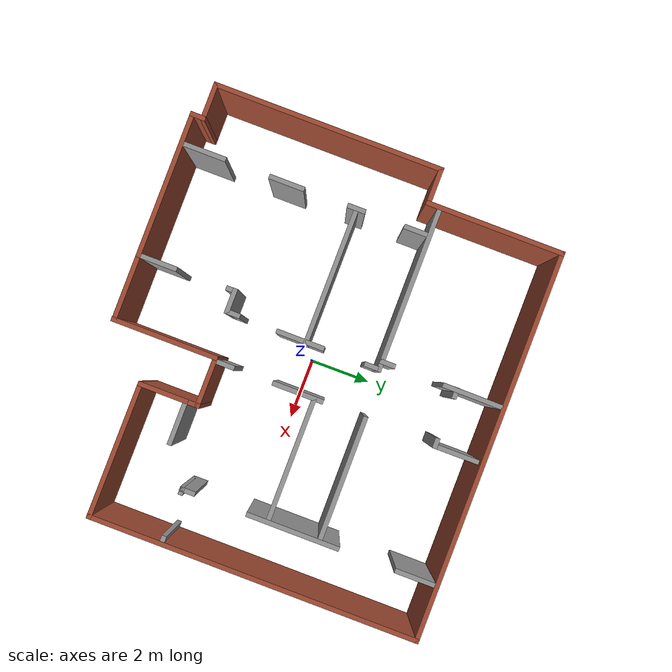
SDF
<?xml version='1.0'?>
<sdf version='1.7'>
  <model name='Building_2'>
    <link name='Wall_0'>
      <pose>0.975539 -4.38291 0 0 0 -1.5708</pose>
      <self_collide>0</self_collide>
      <enable_wind>0</enable_wind>
      <kinematic>0</kinematic>
      <inertial>
        <inertia>
          <ixx>0</ixx>
          <ixy>0</ixy>
          <ixz>0</ixz>
          <iyy>0</iyy>
          <iyz>0</iyz>
          <izz>0</izz>
        </inertia>
        <mass>0</mass>
        <pose>0 0 0 0 -0 0</pose>
      </inertial>
      <visual name='Wall_0_Visual'>
        <pose>0 0 1.25 0 -0 0</pose>
        <geometry>
          <box>
            <size>3.44775 0.15 2.5</size>
          </box>
        </geometry>
        <material>
          <script>
            <uri>file://media/materials/scripts/gazebo.material</uri>
            <name>Gazebo/Bricks</name>
          </script>
          <ambient>1 1 1 1</ambient>
          <shader type='pixel'/>
        </material>
        <meta>
          <layer>0</layer>
        </meta>
        <transparency>0</transparency>
        <cast_shadows>1</cast_shadows>
      </visual>
      <collision name='Wall_0_Collision'>
        <laser_retro>0</laser_retro>
        <max_contacts>10</max_contacts>
        <pose>0 0 1.25 0 -0 0</pose>
        <geometry>
          <box>
            <size>3.44775 0.15 2.5</size>
          </box>
        </geometry>
        <surface>
          <friction>
            <ode>
              <mu>1</mu>
              <mu2>1</mu2>
              <fdir1>0 0 0</fdir1>
              <slip1>0</slip1>
              <slip2>0</slip2>
            </ode>
            <torsional>
              <coefficient>1</coefficient>
              <patch_radius>0</patch_radius>
              <surface_radius>0</surface_radius>
              <use_patch_radius>1</use_patch_radius>
              <ode>
                <slip>0</slip>
              </ode>
            </torsional>
          </friction>
          <bounce>
            <restitution_coefficient>0</restitution_coefficient>
            <threshold>1e+06</threshold>
          </bounce>
          <contact>
            <collide_without_contact>0</collide_without_contact>
            <collide_without_contact_bitmask>1</collide_without_contact_bitmask>
            <collide_bitmask>1</collide_bitmask>
            <ode>
              <soft_cfm>0</soft_cfm>
              <soft_erp>0.2</soft_erp>
              <kp>1e+13</kp>
              <kd>1</kd>
              <max_vel>0.01</max_vel>
              <min_depth>0</min_depth>
            </ode>
            <bullet>
              <split_impulse>1</split_impulse>
              <split_impulse_penetration_threshold>-0.01</split_impulse_penetration_threshold>
              <soft_cfm>0</soft_cfm>
              <soft_erp>0.2</soft_erp>
              <kp>1e+13</kp>
              <kd>1</kd>
            </bullet>
          </contact>
        </surface>
      </collision>
    </link>
    <link name='Wall_1'>
      <pose>-0.074462 -6.02302 0 0 -0 3.14159</pose>
      <self_collide>0</self_collide>
      <enable_wind>0</enable_wind>
      <kinematic>0</kinematic>
      <visual name='Wall_1_Visual'>
        <pose>0 0 1.25 0 -0 0</pose>
        <geometry>
          <box>
            <size>2.25 0.15 2.5</size>
          </box>
        </geometry>
        <material>
          <script>
            <uri>file://media/materials/scripts/gazebo.material</uri>
            <name>Gazebo/Bricks</name>
          </script>
          <ambient>1 1 1 1</ambient>
          <shader type='pixel'/>
        </material>
        <meta>
          <layer>0</layer>
        </meta>
        <transparency>0</transparency>
        <cast_shadows>1</cast_shadows>
      </visual>
      <collision name='Wall_1_Collision'>
        <laser_retro>0</laser_retro>
        <max_contacts>10</max_contacts>
        <pose>0 0 1.25 0 -0 0</pose>
        <geometry>
          <box>
            <size>2.25 0.15 2.5</size>
          </box>
        </geometry>
        <surface>
          <friction>
            <ode>
              <mu>1</mu>
              <mu2>1</mu2>
              <fdir1>0 0 0</fdir1>
              <slip1>0</slip1>
              <slip2>0</slip2>
            </ode>
            <torsional>
              <coefficient>1</coefficient>
              <patch_radius>0</patch_radius>
              <surface_radius>0</surface_radius>
              <use_patch_radius>1</use_patch_radius>
              <ode>
                <slip>0</slip>
              </ode>
            </torsional>
          </friction>
          <bounce>
            <restitution_coefficient>0</restitution_coefficient>
            <threshold>1e+06</threshold>
          </bounce>
          <contact>
            <collide_without_contact>0</collide_without_contact>
            <collide_without_contact_bitmask>1</collide_without_contact_bitmask>
            <collide_bitmask>1</collide_bitmask>
            <ode>
              <soft_cfm>0</soft_cfm>
              <soft_erp>0.2</soft_erp>
              <kp>1e+13</kp>
              <kd>1</kd>
              <max_vel>0.01</max_vel>
              <min_depth>0</min_depth>
            </ode>
            <bullet>
              <split_impulse>1</split_impulse>
              <split_impulse_penetration_threshold>-0.01</split_impulse_penetration_threshold>
              <soft_cfm>0</soft_cfm>
              <soft_erp>0.2</soft_erp>
              <kp>1e+13</kp>
              <kd>1</kd>
            </bullet>
          </contact>
        </surface>
      </collision>
    </link>
    <link name='Wall_10'>
      <pose>-5.72446 3.84994 0 0 -0 1.5708</pose>
      <self_collide>0</self_collide>
      <enable_wind>0</enable_wind>
      <kinematic>0</kinematic>
      <visual name='Wall_10_Visual'>
        <pose>0 0 1.25 0 -0 0</pose>
        <geometry>
          <box>
            <size>4.5 0.15 2.5</size>
          </box>
        </geometry>
        <material>
          <script>
            <uri>file://media/materials/scripts/gazebo.material</uri>
            <name>Gazebo/Bricks</name>
          </script>
          <ambient>1 1 1 1</ambient>
          <shader type='pixel'/>
        </material>
        <meta>
          <layer>0</layer>
        </meta>
        <transparency>0</transparency>
        <cast_shadows>1</cast_shadows>
      </visual>
      <collision name='Wall_10_Collision'>
        <laser_retro>0</laser_retro>
        <max_contacts>10</max_contacts>
        <pose>0 0 1.25 0 -0 0</pose>
        <geometry>
          <box>
            <size>4.5 0.15 2.5</size>
          </box>
        </geometry>
        <surface>
          <friction>
            <ode>
              <mu>1</mu>
              <mu2>1</mu2>
              <fdir1>0 0 0</fdir1>
              <slip1>0</slip1>
              <slip2>0</slip2>
            </ode>
            <torsional>
              <coefficient>1</coefficient>
              <patch_radius>0</patch_radius>
              <surface_radius>0</surface_radius>
              <use_patch_radius>1</use_patch_radius>
              <ode>
                <slip>0</slip>
              </ode>
            </torsional>
          </friction>
          <bounce>
            <restitution_coefficient>0</restitution_coefficient>
            <threshold>1e+06</threshold>
          </bounce>
          <contact>
            <collide_without_contact>0</collide_without_contact>
            <collide_without_contact_bitmask>1</collide_without_contact_bitmask>
            <collide_bitmask>1</collide_bitmask>
            <ode>
              <soft_cfm>0</soft_cfm>
              <soft_erp>0.2</soft_erp>
              <kp>1e+13</kp>
              <kd>1</kd>
              <max_vel>0.01</max_vel>
              <min_depth>0</min_depth>
            </ode>
            <bullet>
              <split_impulse>1</split_impulse>
              <split_impulse_penetration_threshold>-0.01</split_impulse_penetration_threshold>
              <soft_cfm>0</soft_cfm>
              <soft_erp>0.2</soft_erp>
              <kp>1e+13</kp>
              <kd>1</kd>
            </bullet>
          </contact>
        </surface>
      </collision>
    </link>
    <link name='Wall_11'>
      <pose>0.54984 6.01575 0 0 0 -0.001465</pose>
      <self_collide>0</self_collide>
      <enable_wind>0</enable_wind>
      <kinematic>0</kinematic>
      <visual name='Wall_11_Visual'>
        <pose>0 0 1.25 0 -0 0</pose>
        <geometry>
          <box>
            <size>12.6986 0.15 2.5</size>
          </box>
        </geometry>
        <material>
          <script>
            <uri>file://media/materials/scripts/gazebo.material</uri>
            <name>Gazebo/Bricks</name>
          </script>
          <ambient>1 1 1 1</ambient>
          <shader type='pixel'/>
        </material>
        <meta>
          <layer>0</layer>
        </meta>
        <transparency>0</transparency>
        <cast_shadows>1</cast_shadows>
      </visual>
      <collision name='Wall_11_Collision'>
        <laser_retro>0</laser_retro>
        <max_contacts>10</max_contacts>
        <pose>0 0 1.25 0 -0 0</pose>
        <geometry>
          <box>
            <size>12.6986 0.15 2.5</size>
          </box>
        </geometry>
        <surface>
          <friction>
            <ode>
              <mu>1</mu>
              <mu2>1</mu2>
              <fdir1>0 0 0</fdir1>
              <slip1>0</slip1>
              <slip2>0</slip2>
            </ode>
            <torsional>
              <coefficient>1</coefficient>
              <patch_radius>0</patch_radius>
              <surface_radius>0</surface_radius>
              <use_patch_radius>1</use_patch_radius>
              <ode>
                <slip>0</slip>
              </ode>
            </torsional>
          </friction>
          <bounce>
            <restitution_coefficient>0</restitution_coefficient>
            <threshold>1e+06</threshold>
          </bounce>
          <contact>
            <collide_without_contact>0</collide_without_contact>
            <collide_without_contact_bitmask>1</collide_without_contact_bitmask>
            <collide_bitmask>1</collide_bitmask>
            <ode>
              <soft_cfm>0</soft_cfm>
              <soft_erp>0.2</soft_erp>
              <kp>1e+13</kp>
              <kd>1</kd>
              <max_vel>0.01</max_vel>
              <min_depth>0</min_depth>
            </ode>
            <bullet>
              <split_impulse>1</split_impulse>
              <split_impulse_penetration_threshold>-0.01</split_impulse_penetration_threshold>
              <soft_cfm>0</soft_cfm>
              <soft_erp>0.2</soft_erp>
              <kp>1e+13</kp>
              <kd>1</kd>
            </bullet>
          </contact>
        </surface>
      </collision>
    </link>
    <link name='Wall_14'>
      <pose>6.82414 0.706559 0 0 0 -1.5708</pose>
      <self_collide>0</self_collide>
      <enable_wind>0</enable_wind>
      <kinematic>0</kinematic>
      <visual name='Wall_14_Visual'>
        <pose>0 0 1.25 0 -0 0</pose>
        <geometry>
          <box>
            <size>10.75 0.15 2.5</size>
          </box>
        </geometry>
        <material>
          <script>
            <uri>file://media/materials/scripts/gazebo.material</uri>
            <name>Gazebo/Bricks</name>
          </script>
          <ambient>1 1 1 1</ambient>
          <shader type='pixel'/>
        </material>
        <meta>
          <layer>0</layer>
        </meta>
        <transparency>0</transparency>
        <cast_shadows>1</cast_shadows>
      </visual>
      <collision name='Wall_14_Collision'>
        <laser_retro>0</laser_retro>
        <max_contacts>10</max_contacts>
        <pose>0 0 1.25 0 -0 0</pose>
        <geometry>
          <box>
            <size>10.75 0.15 2.5</size>
          </box>
        </geometry>
        <surface>
          <friction>
            <ode>
              <mu>1</mu>
              <mu2>1</mu2>
              <fdir1>0 0 0</fdir1>
              <slip1>0</slip1>
              <slip2>0</slip2>
            </ode>
            <torsional>
              <coefficient>1</coefficient>
              <patch_radius>0</patch_radius>
              <surface_radius>0</surface_radius>
              <use_patch_radius>1</use_patch_radius>
              <ode>
                <slip>0</slip>
              </ode>
            </torsional>
          </friction>
          <bounce>
            <restitution_coefficient>0</restitution_coefficient>
            <threshold>1e+06</threshold>
          </bounce>
          <contact>
            <collide_without_contact>0</collide_without_contact>
            <collide_without_contact_bitmask>1</collide_without_contact_bitmask>
            <collide_bitmask>1</collide_bitmask>
            <ode>
              <soft_cfm>0</soft_cfm>
              <soft_erp>0.2</soft_erp>
              <kp>1e+13</kp>
              <kd>1</kd>
              <max_vel>0.01</max_vel>
              <min_depth>0</min_depth>
            </ode>
            <bullet>
              <split_impulse>1</split_impulse>
              <split_impulse_penetration_threshold>-0.01</split_impulse_penetration_threshold>
              <soft_cfm>0</soft_cfm>
              <soft_erp>0.2</soft_erp>
              <kp>1e+13</kp>
              <kd>1</kd>
            </bullet>
          </contact>
        </surface>
      </collision>
    </link>
    <link name='Wall_15'>
      <pose>4.67484 -4.58425 0 0 -0 3.13732</pose>
      <self_collide>0</self_collide>
      <enable_wind>0</enable_wind>
      <kinematic>0</kinematic>
      <visual name='Wall_15_Visual'>
        <pose>0 0 1.25 0 -0 0</pose>
        <geometry>
          <box>
            <size>4.44864 0.15 2.5</size>
          </box>
        </geometry>
        <material>
          <script>
            <uri>file://media/materials/scripts/gazebo.material</uri>
            <name>Gazebo/Bricks</name>
          </script>
          <ambient>1 1 1 1</ambient>
          <shader type='pixel'/>
        </material>
        <meta>
          <layer>0</layer>
        </meta>
        <transparency>0</transparency>
        <cast_shadows>1</cast_shadows>
      </visual>
      <collision name='Wall_15_Collision'>
        <laser_retro>0</laser_retro>
        <max_contacts>10</max_contacts>
        <pose>0 0 1.25 0 -0 0</pose>
        <geometry>
          <box>
            <size>4.44864 0.15 2.5</size>
          </box>
        </geometry>
        <surface>
          <friction>
            <ode>
              <mu>1</mu>
              <mu2>1</mu2>
              <fdir1>0 0 0</fdir1>
              <slip1>0</slip1>
              <slip2>0</slip2>
            </ode>
            <torsional>
              <coefficient>1</coefficient>
              <patch_radius>0</patch_radius>
              <surface_radius>0</surface_radius>
              <use_patch_radius>1</use_patch_radius>
              <ode>
                <slip>0</slip>
              </ode>
            </torsional>
          </friction>
          <bounce>
            <restitution_coefficient>0</restitution_coefficient>
            <threshold>1e+06</threshold>
          </bounce>
          <contact>
            <collide_without_contact>0</collide_without_contact>
            <collide_without_contact_bitmask>1</collide_without_contact_bitmask>
            <collide_bitmask>1</collide_bitmask>
            <ode>
              <soft_cfm>0</soft_cfm>
              <soft_erp>0.2</soft_erp>
              <kp>1e+13</kp>
              <kd>1</kd>
              <max_vel>0.01</max_vel>
              <min_depth>0</min_depth>
            </ode>
            <bullet>
              <split_impulse>1</split_impulse>
              <split_impulse_penetration_threshold>-0.01</split_impulse_penetration_threshold>
              <soft_cfm>0</soft_cfm>
              <soft_erp>0.2</soft_erp>
              <kp>1e+13</kp>
              <kd>1</kd>
            </bullet>
          </contact>
        </surface>
      </collision>
    </link>
    <link name='Wall_16'>
      <pose>2.52554 -3.64508 0 0 -0 1.5708</pose>
      <self_collide>0</self_collide>
      <enable_wind>0</enable_wind>
      <kinematic>0</kinematic>
      <visual name='Wall_16_Visual'>
        <pose>0 0 1.25 0 -0 0</pose>
        <geometry>
          <box>
            <size>2.00994 0.15 2.5</size>
          </box>
        </geometry>
        <material>
          <script>
            <uri>file://media/materials/scripts/gazebo.material</uri>
            <name>Gazebo/Bricks</name>
          </script>
          <ambient>1 1 1 1</ambient>
          <shader type='pixel'/>
        </material>
        <meta>
          <layer>0</layer>
        </meta>
        <transparency>0</transparency>
        <cast_shadows>1</cast_shadows>
      </visual>
      <collision name='Wall_16_Collision'>
        <laser_retro>0</laser_retro>
        <max_contacts>10</max_contacts>
        <pose>0 0 1.25 0 -0 0</pose>
        <geometry>
          <box>
            <size>2.00994 0.15 2.5</size>
          </box>
        </geometry>
        <surface>
          <friction>
            <ode>
              <mu>1</mu>
              <mu2>1</mu2>
              <fdir1>0 0 0</fdir1>
              <slip1>0</slip1>
              <slip2>0</slip2>
            </ode>
            <torsional>
              <coefficient>1</coefficient>
              <patch_radius>0</patch_radius>
              <surface_radius>0</surface_radius>
              <use_patch_radius>1</use_patch_radius>
              <ode>
                <slip>0</slip>
              </ode>
            </torsional>
          </friction>
          <bounce>
            <restitution_coefficient>0</restitution_coefficient>
            <threshold>1e+06</threshold>
          </bounce>
          <contact>
            <collide_without_contact>0</collide_without_contact>
            <collide_without_contact_bitmask>1</collide_without_contact_bitmask>
            <collide_bitmask>1</collide_bitmask>
            <ode>
              <soft_cfm>0</soft_cfm>
              <soft_erp>0.2</soft_erp>
              <kp>1e+13</kp>
              <kd>1</kd>
              <max_vel>0.01</max_vel>
              <min_depth>0</min_depth>
            </ode>
            <bullet>
              <split_impulse>1</split_impulse>
              <split_impulse_penetration_threshold>-0.01</split_impulse_penetration_threshold>
              <soft_cfm>0</soft_cfm>
              <soft_erp>0.2</soft_erp>
              <kp>1e+13</kp>
              <kd>1</kd>
            </bullet>
          </contact>
        </surface>
      </collision>
    </link>
    <link name='Wall_17'>
      <pose>1.75059 -2.71926 0 0 -0 3.14053</pose>
      <self_collide>0</self_collide>
      <enable_wind>0</enable_wind>
      <kinematic>0</kinematic>
      <visual name='Wall_17_Visual'>
        <pose>0 0 1.25 0 -0 0</pose>
        <geometry>
          <box>
            <size>1.69991 0.15 2.5</size>
          </box>
        </geometry>
        <material>
          <script>
            <uri>file://media/materials/scripts/gazebo.material</uri>
            <name>Gazebo/Bricks</name>
          </script>
          <ambient>1 1 1 1</ambient>
          <shader type='pixel'/>
        </material>
        <meta>
          <layer>0</layer>
        </meta>
        <transparency>0</transparency>
        <cast_shadows>1</cast_shadows>
      </visual>
      <collision name='Wall_17_Collision'>
        <laser_retro>0</laser_retro>
        <max_contacts>10</max_contacts>
        <pose>0 0 1.25 0 -0 0</pose>
        <geometry>
          <box>
            <size>1.69991 0.15 2.5</size>
          </box>
        </geometry>
        <surface>
          <friction>
            <ode>
              <mu>1</mu>
              <mu2>1</mu2>
              <fdir1>0 0 0</fdir1>
              <slip1>0</slip1>
              <slip2>0</slip2>
            </ode>
            <torsional>
              <coefficient>1</coefficient>
              <patch_radius>0</patch_radius>
              <surface_radius>0</surface_radius>
              <use_patch_radius>1</use_patch_radius>
              <ode>
                <slip>0</slip>
              </ode>
            </torsional>
          </friction>
          <bounce>
            <restitution_coefficient>0</restitution_coefficient>
            <threshold>1e+06</threshold>
          </bounce>
          <contact>
            <collide_without_contact>0</collide_without_contact>
            <collide_without_contact_bitmask>1</collide_without_contact_bitmask>
            <collide_bitmask>1</collide_bitmask>
            <ode>
              <soft_cfm>0</soft_cfm>
              <soft_erp>0.2</soft_erp>
              <kp>1e+13</kp>
              <kd>1</kd>
              <max_vel>0.01</max_vel>
              <min_depth>0</min_depth>
            </ode>
            <bullet>
              <split_impulse>1</split_impulse>
              <split_impulse_penetration_threshold>-0.01</split_impulse_penetration_threshold>
              <soft_cfm>0</soft_cfm>
              <soft_erp>0.2</soft_erp>
              <kp>1e+13</kp>
              <kd>1</kd>
            </bullet>
          </contact>
        </surface>
      </collision>
    </link>
    <link name='Wall_19'>
      <pose>-4.78364 -5.32139 0 0 -0 1.5708</pose>
      <self_collide>0</self_collide>
      <enable_wind>0</enable_wind>
      <kinematic>0</kinematic>
      <visual name='Wall_19_Visual'>
        <pose>0 0 1.25 0 -0 0</pose>
        <geometry>
          <box>
            <size>1.5 0.15 2.5</size>
          </box>
        </geometry>
        <material>
          <script>
            <uri>file://media/materials/scripts/gazebo.material</uri>
            <name>Gazebo/Grey</name>
          </script>
          <ambient>1 1 1 1</ambient>
          <shader type='pixel'/>
        </material>
        <meta>
          <layer>0</layer>
        </meta>
        <transparency>0</transparency>
        <cast_shadows>1</cast_shadows>
      </visual>
      <collision name='Wall_19_Collision'>
        <laser_retro>0</laser_retro>
        <max_contacts>10</max_contacts>
        <pose>0 0 1.25 0 -0 0</pose>
        <geometry>
          <box>
            <size>1.5 0.15 2.5</size>
          </box>
        </geometry>
        <surface>
          <friction>
            <ode>
              <mu>1</mu>
              <mu2>1</mu2>
              <fdir1>0 0 0</fdir1>
              <slip1>0</slip1>
              <slip2>0</slip2>
            </ode>
            <torsional>
              <coefficient>1</coefficient>
              <patch_radius>0</patch_radius>
              <surface_radius>0</surface_radius>
              <use_patch_radius>1</use_patch_radius>
              <ode>
                <slip>0</slip>
              </ode>
            </torsional>
          </friction>
          <bounce>
            <restitution_coefficient>0</restitution_coefficient>
            <threshold>1e+06</threshold>
          </bounce>
          <contact>
            <collide_without_contact>0</collide_without_contact>
            <collide_without_contact_bitmask>1</collide_without_contact_bitmask>
            <collide_bitmask>1</collide_bitmask>
            <ode>
              <soft_cfm>0</soft_cfm>
              <soft_erp>0.2</soft_erp>
              <kp>1e+13</kp>
              <kd>1</kd>
              <max_vel>0.01</max_vel>
              <min_depth>0</min_depth>
            </ode>
            <bullet>
              <split_impulse>1</split_impulse>
              <split_impulse_penetration_threshold>-0.01</split_impulse_penetration_threshold>
              <soft_cfm>0</soft_cfm>
              <soft_erp>0.2</soft_erp>
              <kp>1e+13</kp>
              <kd>1</kd>
            </bullet>
          </contact>
        </surface>
      </collision>
    </link>
    <link name='Wall_23'>
      <pose>-4.77837 -2.58462 0 0 -0 1.5708</pose>
      <self_collide>0</self_collide>
      <enable_wind>0</enable_wind>
      <kinematic>0</kinematic>
      <inertial>
        <inertia>
          <ixx>0</ixx>
          <ixy>0</ixy>
          <ixz>0</ixz>
          <iyy>0</iyy>
          <iyz>0</iyz>
          <izz>0</izz>
        </inertia>
        <mass>0</mass>
        <pose>0 0 0 0 -0 0</pose>
      </inertial>
      <visual name='Wall_23_Visual'>
        <pose>0 0 1.25 0 -0 0</pose>
        <geometry>
          <box>
            <size>1.15111 0.15 2.5</size>
          </box>
        </geometry>
        <material>
          <script>
            <uri>file://media/materials/scripts/gazebo.material</uri>
            <name>Gazebo/Grey</name>
          </script>
          <ambient>1 1 1 1</ambient>
          <shader type='pixel'/>
        </material>
        <meta>
          <layer>0</layer>
        </meta>
        <transparency>0</transparency>
        <cast_shadows>1</cast_shadows>
      </visual>
      <collision name='Wall_23_Collision'>
        <laser_retro>0</laser_retro>
        <max_contacts>10</max_contacts>
        <pose>0 0 1.25 0 -0 0</pose>
        <geometry>
          <box>
            <size>1.15111 0.15 2.5</size>
          </box>
        </geometry>
        <surface>
          <friction>
            <ode>
              <mu>1</mu>
              <mu2>1</mu2>
              <fdir1>0 0 0</fdir1>
              <slip1>0</slip1>
              <slip2>0</slip2>
            </ode>
            <torsional>
              <coefficient>1</coefficient>
              <patch_radius>0</patch_radius>
              <surface_radius>0</surface_radius>
              <use_patch_radius>1</use_patch_radius>
              <ode>
                <slip>0</slip>
              </ode>
            </torsional>
          </friction>
          <bounce>
            <restitution_coefficient>0</restitution_coefficient>
            <threshold>1e+06</threshold>
          </bounce>
          <contact>
            <collide_without_contact>0</collide_without_contact>
            <collide_without_contact_bitmask>1</collide_without_contact_bitmask>
            <collide_bitmask>1</collide_bitmask>
            <ode>
              <soft_cfm>0</soft_cfm>
              <soft_erp>0.2</soft_erp>
              <kp>1e+13</kp>
              <kd>1</kd>
              <max_vel>0.01</max_vel>
              <min_depth>0</min_depth>
            </ode>
            <bullet>
              <split_impulse>1</split_impulse>
              <split_impulse_penetration_threshold>-0.01</split_impulse_penetration_threshold>
              <soft_cfm>0</soft_cfm>
              <soft_erp>0.2</soft_erp>
              <kp>1e+13</kp>
              <kd>1</kd>
            </bullet>
          </contact>
        </surface>
      </collision>
    </link>
    <link name='Wall_25'>
      <pose>-4.79341 -0.321482 0 0 -0 1.5708</pose>
      <self_collide>0</self_collide>
      <enable_wind>0</enable_wind>
      <kinematic>0</kinematic>
      <visual name='Wall_25_Visual'>
        <pose>0 0 1.25 0 -0 0</pose>
        <geometry>
          <box>
            <size>0.586087 0.15 2.5</size>
          </box>
        </geometry>
        <material>
          <script>
            <uri>file://media/materials/scripts/gazebo.material</uri>
            <name>Gazebo/Grey</name>
          </script>
          <ambient>1 1 1 1</ambient>
          <shader type='pixel'/>
        </material>
        <meta>
          <layer>0</layer>
        </meta>
        <transparency>0</transparency>
        <cast_shadows>1</cast_shadows>
      </visual>
      <collision name='Wall_25_Collision'>
        <laser_retro>0</laser_retro>
        <max_contacts>10</max_contacts>
        <pose>0 0 1.25 0 -0 0</pose>
        <geometry>
          <box>
            <size>0.586087 0.15 2.5</size>
          </box>
        </geometry>
        <surface>
          <friction>
            <ode>
              <mu>1</mu>
              <mu2>1</mu2>
              <fdir1>0 0 0</fdir1>
              <slip1>0</slip1>
              <slip2>0</slip2>
            </ode>
            <torsional>
              <coefficient>1</coefficient>
              <patch_radius>0</patch_radius>
              <surface_radius>0</surface_radius>
              <use_patch_radius>1</use_patch_radius>
              <ode>
                <slip>0</slip>
              </ode>
            </torsional>
          </friction>
          <bounce>
            <restitution_coefficient>0</restitution_coefficient>
            <threshold>1e+06</threshold>
          </bounce>
          <contact>
            <collide_without_contact>0</collide_without_contact>
            <collide_without_contact_bitmask>1</collide_without_contact_bitmask>
            <collide_bitmask>1</collide_bitmask>
            <ode>
              <soft_cfm>0</soft_cfm>
              <soft_erp>0.2</soft_erp>
              <kp>1e+13</kp>
              <kd>1</kd>
              <max_vel>0.01</max_vel>
              <min_depth>0</min_depth>
            </ode>
            <bullet>
              <split_impulse>1</split_impulse>
              <split_impulse_penetration_threshold>-0.01</split_impulse_penetration_threshold>
              <soft_cfm>0</soft_cfm>
              <soft_erp>0.2</soft_erp>
              <kp>1e+13</kp>
              <kd>1</kd>
            </bullet>
          </contact>
        </surface>
      </collision>
    </link>
    <link name='Wall_27'>
      <pose>-4.80309 1.60581 0 0 -0 1.5708</pose>
      <self_collide>0</self_collide>
      <enable_wind>0</enable_wind>
      <kinematic>0</kinematic>
      <inertial>
        <inertia>
          <ixx>0</ixx>
          <ixy>0</ixy>
          <ixz>0</ixz>
          <iyy>0</iyy>
          <iyz>0</iyz>
          <izz>0</izz>
        </inertia>
        <mass>0</mass>
        <pose>0 0 0 0 -0 0</pose>
      </inertial>
      <visual name='Wall_27_Visual'>
        <pose>0 0 1.25 0 -0 0</pose>
        <geometry>
          <box>
            <size>0.757541 0.15 2.5</size>
          </box>
        </geometry>
        <material>
          <script>
            <uri>file://media/materials/scripts/gazebo.material</uri>
            <name>Gazebo/Grey</name>
          </script>
          <ambient>1 1 1 1</ambient>
          <shader type='pixel'/>
        </material>
        <meta>
          <layer>0</layer>
        </meta>
        <transparency>0</transparency>
        <cast_shadows>1</cast_shadows>
      </visual>
      <collision name='Wall_27_Collision'>
        <laser_retro>0</laser_retro>
        <max_contacts>10</max_contacts>
        <pose>0 0 1.25 0 -0 0</pose>
        <geometry>
          <box>
            <size>0.757541 0.15 2.5</size>
          </box>
        </geometry>
        <surface>
          <friction>
            <ode>
              <mu>1</mu>
              <mu2>1</mu2>
              <fdir1>0 0 0</fdir1>
              <slip1>0</slip1>
              <slip2>0</slip2>
            </ode>
            <torsional>
              <coefficient>1</coefficient>
              <patch_radius>0</patch_radius>
              <surface_radius>0</surface_radius>
              <use_patch_radius>1</use_patch_radius>
              <ode>
                <slip>0</slip>
              </ode>
            </torsional>
          </friction>
          <bounce>
            <restitution_coefficient>0</restitution_coefficient>
            <threshold>1e+06</threshold>
          </bounce>
          <contact>
            <collide_without_contact>0</collide_without_contact>
            <collide_without_contact_bitmask>1</collide_without_contact_bitmask>
            <collide_bitmask>1</collide_bitmask>
            <ode>
              <soft_cfm>0</soft_cfm>
              <soft_erp>0.2</soft_erp>
              <kp>1e+13</kp>
              <kd>1</kd>
              <max_vel>0.01</max_vel>
              <min_depth>0</min_depth>
            </ode>
            <bullet>
              <split_impulse>1</split_impulse>
              <split_impulse_penetration_threshold>-0.01</split_impulse_penetration_threshold>
              <soft_cfm>0</soft_cfm>
              <soft_erp>0.2</soft_erp>
              <kp>1e+13</kp>
              <kd>1</kd>
            </bullet>
          </contact>
        </surface>
      </collision>
    </link>
    <link name='Wall_29'>
      <pose>-3.01821 2.05691 0 0 -0 0</pose>
      <self_collide>0</self_collide>
      <enable_wind>0</enable_wind>
      <kinematic>0</kinematic>
      <inertial>
        <inertia>
          <ixx>0</ixx>
          <ixy>0</ixy>
          <ixz>0</ixz>
          <iyy>0</iyy>
          <iyz>0</iyz>
          <izz>0</izz>
        </inertia>
        <mass>0</mass>
        <pose>0 0 0 0 -0 0</pose>
      </inertial>
      <visual name='Wall_29_Visual'>
        <pose>0 0 1.25 0 -0 0</pose>
        <geometry>
          <box>
            <size>5.27655 0.15 2.5</size>
          </box>
        </geometry>
        <material>
          <script>
            <uri>file://media/materials/scripts/gazebo.material</uri>
            <name>Gazebo/Grey</name>
          </script>
          <ambient>1 1 1 1</ambient>
          <shader type='pixel'/>
        </material>
        <meta>
          <layer>0</layer>
        </meta>
        <transparency>0</transparency>
        <cast_shadows>1</cast_shadows>
      </visual>
      <collision name='Wall_29_Collision'>
        <laser_retro>0</laser_retro>
        <max_contacts>10</max_contacts>
        <pose>0 0 1.25 0 -0 0</pose>
        <geometry>
          <box>
            <size>5.27655 0.15 2.5</size>
          </box>
        </geometry>
        <surface>
          <friction>
            <ode>
              <mu>1</mu>
              <mu2>1</mu2>
              <fdir1>0 0 0</fdir1>
              <slip1>0</slip1>
              <slip2>0</slip2>
            </ode>
            <torsional>
              <coefficient>1</coefficient>
              <patch_radius>0</patch_radius>
              <surface_radius>0</surface_radius>
              <use_patch_radius>1</use_patch_radius>
              <ode>
                <slip>0</slip>
              </ode>
            </torsional>
          </friction>
          <bounce>
            <restitution_coefficient>0</restitution_coefficient>
            <threshold>1e+06</threshold>
          </bounce>
          <contact>
            <collide_without_contact>0</collide_without_contact>
            <collide_without_contact_bitmask>1</collide_without_contact_bitmask>
            <collide_bitmask>1</collide_bitmask>
            <ode>
              <soft_cfm>0</soft_cfm>
              <soft_erp>0.2</soft_erp>
              <kp>1e+13</kp>
              <kd>1</kd>
              <max_vel>0.01</max_vel>
              <min_depth>0</min_depth>
            </ode>
            <bullet>
              <split_impulse>1</split_impulse>
              <split_impulse_penetration_threshold>-0.01</split_impulse_penetration_threshold>
              <soft_cfm>0</soft_cfm>
              <soft_erp>0.2</soft_erp>
              <kp>1e+13</kp>
              <kd>1</kd>
            </bullet>
          </contact>
        </surface>
      </collision>
    </link>
    <link name='Wall_30'>
      <pose>-0.459211 1.7956 0 0 0 -1.5708</pose>
      <self_collide>0</self_collide>
      <enable_wind>0</enable_wind>
      <kinematic>0</kinematic>
      <inertial>
        <inertia>
          <ixx>0</ixx>
          <ixy>0</ixy>
          <ixz>0</ixz>
          <iyy>0</iyy>
          <iyz>0</iyz>
          <izz>0</izz>
        </inertia>
        <mass>0</mass>
        <pose>0 0 0 0 -0 0</pose>
      </inertial>
      <visual name='Wall_30_Visual'>
        <pose>0 0 1.25 0 -0 0</pose>
        <geometry>
          <box>
            <size>0.445654 0.15 2.5</size>
          </box>
        </geometry>
        <material>
          <script>
            <uri>file://media/materials/scripts/gazebo.material</uri>
            <name>Gazebo/Grey</name>
          </script>
          <ambient>1 1 1 1</ambient>
          <shader type='pixel'/>
        </material>
        <meta>
          <layer>0</layer>
        </meta>
        <transparency>0</transparency>
        <cast_shadows>1</cast_shadows>
      </visual>
      <collision name='Wall_30_Collision'>
        <laser_retro>0</laser_retro>
        <max_contacts>10</max_contacts>
        <pose>0 0 1.25 0 -0 0</pose>
        <geometry>
          <box>
            <size>0.445654 0.15 2.5</size>
          </box>
        </geometry>
        <surface>
          <friction>
            <ode>
              <mu>1</mu>
              <mu2>1</mu2>
              <fdir1>0 0 0</fdir1>
              <slip1>0</slip1>
              <slip2>0</slip2>
            </ode>
            <torsional>
              <coefficient>1</coefficient>
              <patch_radius>0</patch_radius>
              <surface_radius>0</surface_radius>
              <use_patch_radius>1</use_patch_radius>
              <ode>
                <slip>0</slip>
              </ode>
            </torsional>
          </friction>
          <bounce>
            <restitution_coefficient>0</restitution_coefficient>
            <threshold>1e+06</threshold>
          </bounce>
          <contact>
            <collide_without_contact>0</collide_without_contact>
            <collide_without_contact_bitmask>1</collide_without_contact_bitmask>
            <collide_bitmask>1</collide_bitmask>
            <ode>
              <soft_cfm>0</soft_cfm>
              <soft_erp>0.2</soft_erp>
              <kp>1e+13</kp>
              <kd>1</kd>
              <max_vel>0.01</max_vel>
              <min_depth>0</min_depth>
            </ode>
            <bullet>
              <split_impulse>1</split_impulse>
              <split_impulse_penetration_threshold>-0.01</split_impulse_penetration_threshold>
              <soft_cfm>0</soft_cfm>
              <soft_erp>0.2</soft_erp>
              <kp>1e+13</kp>
              <kd>1</kd>
            </bullet>
          </contact>
        </surface>
      </collision>
    </link>
    <link name='Wall_33'>
      <pose>-0.445665 -0.504153 0 0 0 -1.5708</pose>
      <self_collide>0</self_collide>
      <enable_wind>0</enable_wind>
      <kinematic>0</kinematic>
      <inertial>
        <inertia>
          <ixx>0</ixx>
          <ixy>0</ixy>
          <ixz>0</ixz>
          <iyy>0</iyy>
          <iyz>0</iyz>
          <izz>0</izz>
        </inertia>
        <mass>0</mass>
        <pose>0 0 0 0 -0 0</pose>
      </inertial>
      <visual name='Wall_33_Visual'>
        <pose>0 0 1.25 0 -0 0</pose>
        <geometry>
          <box>
            <size>1.56049 0.15 2.5</size>
          </box>
        </geometry>
        <material>
          <script>
            <uri>file://media/materials/scripts/gazebo.material</uri>
            <name>Gazebo/Grey</name>
          </script>
          <ambient>1 1 1 1</ambient>
          <shader type='pixel'/>
        </material>
        <meta>
          <layer>0</layer>
        </meta>
        <transparency>0</transparency>
        <cast_shadows>1</cast_shadows>
      </visual>
      <collision name='Wall_33_Collision'>
        <laser_retro>0</laser_retro>
        <max_contacts>10</max_contacts>
        <pose>0 0 1.25 0 -0 0</pose>
        <geometry>
          <box>
            <size>1.56049 0.15 2.5</size>
          </box>
        </geometry>
        <surface>
          <friction>
            <ode>
              <mu>1</mu>
              <mu2>1</mu2>
              <fdir1>0 0 0</fdir1>
              <slip1>0</slip1>
              <slip2>0</slip2>
            </ode>
            <torsional>
              <coefficient>1</coefficient>
              <patch_radius>0</patch_radius>
              <surface_radius>0</surface_radius>
              <use_patch_radius>1</use_patch_radius>
              <ode>
                <slip>0</slip>
              </ode>
            </torsional>
          </friction>
          <bounce>
            <restitution_coefficient>0</restitution_coefficient>
            <threshold>1e+06</threshold>
          </bounce>
          <contact>
            <collide_without_contact>0</collide_without_contact>
            <collide_without_contact_bitmask>1</collide_without_contact_bitmask>
            <collide_bitmask>1</collide_bitmask>
            <ode>
              <soft_cfm>0</soft_cfm>
              <soft_erp>0.2</soft_erp>
              <kp>1e+13</kp>
              <kd>1</kd>
              <max_vel>0.01</max_vel>
              <min_depth>0</min_depth>
            </ode>
            <bullet>
              <split_impulse>1</split_impulse>
              <split_impulse_penetration_threshold>-0.01</split_impulse_penetration_threshold>
              <soft_cfm>0</soft_cfm>
              <soft_erp>0.2</soft_erp>
              <kp>1e+13</kp>
              <kd>1</kd>
            </bullet>
          </contact>
        </surface>
      </collision>
    </link>
    <link name='Wall_36'>
      <pose>-2.55225 -0.313301 0 0 -0 3.14002</pose>
      <self_collide>0</self_collide>
      <enable_wind>0</enable_wind>
      <kinematic>0</kinematic>
      <inertial>
        <inertia>
          <ixx>0</ixx>
          <ixy>0</ixy>
          <ixz>0</ixz>
          <iyy>0</iyy>
          <iyz>0</iyz>
          <izz>0</izz>
        </inertia>
        <mass>0</mass>
        <pose>0 0 0 0 -0 0</pose>
      </inertial>
      <visual name='Wall_36_Visual'>
        <pose>0 0 1.25 0 -0 0</pose>
        <geometry>
          <box>
            <size>4.36835 0.15 2.5</size>
          </box>
        </geometry>
        <material>
          <script>
            <uri>file://media/materials/scripts/gazebo.material</uri>
            <name>Gazebo/Grey</name>
          </script>
          <ambient>1 1 1 1</ambient>
          <shader type='pixel'/>
        </material>
        <meta>
          <layer>0</layer>
        </meta>
        <transparency>0</transparency>
        <cast_shadows>1</cast_shadows>
      </visual>
      <collision name='Wall_36_Collision'>
        <laser_retro>0</laser_retro>
        <max_contacts>10</max_contacts>
        <pose>0 0 1.25 0 -0 0</pose>
        <geometry>
          <box>
            <size>4.36835 0.15 2.5</size>
          </box>
        </geometry>
        <surface>
          <friction>
            <ode>
              <mu>1</mu>
              <mu2>1</mu2>
              <fdir1>0 0 0</fdir1>
              <slip1>0</slip1>
              <slip2>0</slip2>
            </ode>
            <torsional>
              <coefficient>1</coefficient>
              <patch_radius>0</patch_radius>
              <surface_radius>0</surface_radius>
              <use_patch_radius>1</use_patch_radius>
              <ode>
                <slip>0</slip>
              </ode>
            </torsional>
          </friction>
          <bounce>
            <restitution_coefficient>0</restitution_coefficient>
            <threshold>1e+06</threshold>
          </bounce>
          <contact>
            <collide_without_contact>0</collide_without_contact>
            <collide_without_contact_bitmask>1</collide_without_contact_bitmask>
            <collide_bitmask>1</collide_bitmask>
            <ode>
              <soft_cfm>0</soft_cfm>
              <soft_erp>0.2</soft_erp>
              <kp>1e+13</kp>
              <kd>1</kd>
              <max_vel>0.01</max_vel>
              <min_depth>0</min_depth>
            </ode>
            <bullet>
              <split_impulse>1</split_impulse>
              <split_impulse_penetration_threshold>-0.01</split_impulse_penetration_threshold>
              <soft_cfm>0</soft_cfm>
              <soft_erp>0.2</soft_erp>
              <kp>1e+13</kp>
              <kd>1</kd>
            </bullet>
          </contact>
        </surface>
      </collision>
    </link>
    <link name='Wall_42'>
      <pose>-1.1239 -5.36388 0 0 -0 1.56899</pose>
      <self_collide>0</self_collide>
      <enable_wind>0</enable_wind>
      <kinematic>0</kinematic>
      <inertial>
        <inertia>
          <ixx>0</ixx>
          <ixy>0</ixy>
          <ixz>0</ixz>
          <iyy>0</iyy>
          <iyz>0</iyz>
          <izz>0</izz>
        </inertia>
        <mass>0</mass>
        <pose>0 0 0 0 -0 0</pose>
      </inertial>
      <visual name='Wall_42_Visual'>
        <pose>0 0 1.25 0 -0 0</pose>
        <geometry>
          <box>
            <size>1.1746 0.15 2.5</size>
          </box>
        </geometry>
        <material>
          <script>
            <uri>file://media/materials/scripts/gazebo.material</uri>
            <name>Gazebo/Grey</name>
          </script>
          <ambient>1 1 1 1</ambient>
          <shader type='pixel'/>
        </material>
        <meta>
          <layer>0</layer>
        </meta>
        <transparency>0</transparency>
        <cast_shadows>1</cast_shadows>
      </visual>
      <collision name='Wall_42_Collision'>
        <laser_retro>0</laser_retro>
        <max_contacts>10</max_contacts>
        <pose>0 0 1.25 0 -0 0</pose>
        <geometry>
          <box>
            <size>1.1746 0.15 2.5</size>
          </box>
        </geometry>
        <surface>
          <friction>
            <ode>
              <mu>1</mu>
              <mu2>1</mu2>
              <fdir1>0 0 0</fdir1>
              <slip1>0</slip1>
              <slip2>0</slip2>
            </ode>
            <torsional>
              <coefficient>1</coefficient>
              <patch_radius>0</patch_radius>
              <surface_radius>0</surface_radius>
              <use_patch_radius>1</use_patch_radius>
              <ode>
                <slip>0</slip>
              </ode>
            </torsional>
          </friction>
          <bounce>
            <restitution_coefficient>0</restitution_coefficient>
            <threshold>1e+06</threshold>
          </bounce>
          <contact>
            <collide_without_contact>0</collide_without_contact>
            <collide_without_contact_bitmask>1</collide_without_contact_bitmask>
            <collide_bitmask>1</collide_bitmask>
            <ode>
              <soft_cfm>0</soft_cfm>
              <soft_erp>0.2</soft_erp>
              <kp>1e+13</kp>
              <kd>1</kd>
              <max_vel>0.01</max_vel>
              <min_depth>0</min_depth>
            </ode>
            <bullet>
              <split_impulse>1</split_impulse>
              <split_impulse_penetration_threshold>-0.01</split_impulse_penetration_threshold>
              <soft_cfm>0</soft_cfm>
              <soft_erp>0.2</soft_erp>
              <kp>1e+13</kp>
              <kd>1</kd>
            </bullet>
          </contact>
        </surface>
      </collision>
    </link>
    <link name='Wall_44'>
      <pose>-1.13344 -3.07085 0 0 -0 1.5708</pose>
      <self_collide>0</self_collide>
      <enable_wind>0</enable_wind>
      <kinematic>0</kinematic>
      <inertial>
        <inertia>
          <ixx>0</ixx>
          <ixy>0</ixy>
          <ixz>0</ixz>
          <iyy>0</iyy>
          <iyz>0</iyz>
          <izz>0</izz>
        </inertia>
        <mass>0</mass>
        <pose>0 0 0 0 -0 0</pose>
      </inertial>
      <visual name='Wall_44_Visual'>
        <pose>0 0 1.25 0 -0 0</pose>
        <geometry>
          <box>
            <size>0.209166 0.15 2.5</size>
          </box>
        </geometry>
        <material>
          <script>
            <uri>file://media/materials/scripts/gazebo.material</uri>
            <name>Gazebo/Grey</name>
          </script>
          <ambient>1 1 1 1</ambient>
          <shader type='pixel'/>
        </material>
        <meta>
          <layer>0</layer>
        </meta>
        <transparency>0</transparency>
        <cast_shadows>1</cast_shadows>
      </visual>
      <collision name='Wall_44_Collision'>
        <laser_retro>0</laser_retro>
        <max_contacts>10</max_contacts>
        <pose>0 0 1.25 0 -0 0</pose>
        <geometry>
          <box>
            <size>0.209166 0.15 2.5</size>
          </box>
        </geometry>
        <surface>
          <friction>
            <ode>
              <mu>1</mu>
              <mu2>1</mu2>
              <fdir1>0 0 0</fdir1>
              <slip1>0</slip1>
              <slip2>0</slip2>
            </ode>
            <torsional>
              <coefficient>1</coefficient>
              <patch_radius>0</patch_radius>
              <surface_radius>0</surface_radius>
              <use_patch_radius>1</use_patch_radius>
              <ode>
                <slip>0</slip>
              </ode>
            </torsional>
          </friction>
          <bounce>
            <restitution_coefficient>0</restitution_coefficient>
            <threshold>1e+06</threshold>
          </bounce>
          <contact>
            <collide_without_contact>0</collide_without_contact>
            <collide_without_contact_bitmask>1</collide_without_contact_bitmask>
            <collide_bitmask>1</collide_bitmask>
            <ode>
              <soft_cfm>0</soft_cfm>
              <soft_erp>0.2</soft_erp>
              <kp>1e+13</kp>
              <kd>1</kd>
              <max_vel>0.01</max_vel>
              <min_depth>0</min_depth>
            </ode>
            <bullet>
              <split_impulse>1</split_impulse>
              <split_impulse_penetration_threshold>-0.01</split_impulse_penetration_threshold>
              <soft_cfm>0</soft_cfm>
              <soft_erp>0.2</soft_erp>
              <kp>1e+13</kp>
              <kd>1</kd>
            </bullet>
          </contact>
        </surface>
      </collision>
    </link>
    <link name='Wall_45'>
      <pose>-0.801988 -2.89585 0 0 -0 0</pose>
      <self_collide>0</self_collide>
      <enable_wind>0</enable_wind>
      <kinematic>0</kinematic>
      <inertial>
        <inertia>
          <ixx>0</ixx>
          <ixy>0</ixy>
          <ixz>0</ixz>
          <iyy>0</iyy>
          <iyz>0</iyz>
          <izz>0</izz>
        </inertia>
        <mass>0</mass>
        <pose>0 0 0 0 -0 0</pose>
      </inertial>
      <visual name='Wall_45_Visual'>
        <pose>0 0 1.25 0 -0 0</pose>
        <geometry>
          <box>
            <size>0.822962 0.15 2.5</size>
          </box>
        </geometry>
        <material>
          <script>
            <uri>file://media/materials/scripts/gazebo.material</uri>
            <name>Gazebo/Grey</name>
          </script>
          <ambient>1 1 1 1</ambient>
          <shader type='pixel'/>
        </material>
        <meta>
          <layer>0</layer>
        </meta>
        <transparency>0</transparency>
        <cast_shadows>1</cast_shadows>
      </visual>
      <collision name='Wall_45_Collision'>
        <laser_retro>0</laser_retro>
        <max_contacts>10</max_contacts>
        <pose>0 0 1.25 0 -0 0</pose>
        <geometry>
          <box>
            <size>0.822962 0.15 2.5</size>
          </box>
        </geometry>
        <surface>
          <friction>
            <ode>
              <mu>1</mu>
              <mu2>1</mu2>
              <fdir1>0 0 0</fdir1>
              <slip1>0</slip1>
              <slip2>0</slip2>
            </ode>
            <torsional>
              <coefficient>1</coefficient>
              <patch_radius>0</patch_radius>
              <surface_radius>0</surface_radius>
              <use_patch_radius>1</use_patch_radius>
              <ode>
                <slip>0</slip>
              </ode>
            </torsional>
          </friction>
          <bounce>
            <restitution_coefficient>0</restitution_coefficient>
            <threshold>1e+06</threshold>
          </bounce>
          <contact>
            <collide_without_contact>0</collide_without_contact>
            <collide_without_contact_bitmask>1</collide_without_contact_bitmask>
            <collide_bitmask>1</collide_bitmask>
            <ode>
              <soft_cfm>0</soft_cfm>
              <soft_erp>0.2</soft_erp>
              <kp>1e+13</kp>
              <kd>1</kd>
              <max_vel>0.01</max_vel>
              <min_depth>0</min_depth>
            </ode>
            <bullet>
              <split_impulse>1</split_impulse>
              <split_impulse_penetration_threshold>-0.01</split_impulse_penetration_threshold>
              <soft_cfm>0</soft_cfm>
              <soft_erp>0.2</soft_erp>
              <kp>1e+13</kp>
              <kd>1</kd>
            </bullet>
          </contact>
        </surface>
      </collision>
    </link>
    <link name='Wall_46'>
      <pose>-0.467072 -2.72031 0 0 -0 1.5708</pose>
      <self_collide>0</self_collide>
      <enable_wind>0</enable_wind>
      <kinematic>0</kinematic>
      <visual name='Wall_46_Visual'>
        <pose>0 0 1.25 0 -0 0</pose>
        <geometry>
          <box>
            <size>0.5 0.15 2.5</size>
          </box>
        </geometry>
        <material>
          <script>
            <uri>file://media/materials/scripts/gazebo.material</uri>
            <name>Gazebo/Grey</name>
          </script>
          <ambient>1 1 1 1</ambient>
          <shader type='pixel'/>
        </material>
        <meta>
          <layer>0</layer>
        </meta>
        <transparency>0</transparency>
        <cast_shadows>1</cast_shadows>
      </visual>
      <collision name='Wall_46_Collision'>
        <laser_retro>0</laser_retro>
        <max_contacts>10</max_contacts>
        <pose>0 0 1.25 0 -0 0</pose>
        <geometry>
          <box>
            <size>0.5 0.15 2.5</size>
          </box>
        </geometry>
        <surface>
          <friction>
            <ode>
              <mu>1</mu>
              <mu2>1</mu2>
              <fdir1>0 0 0</fdir1>
              <slip1>0</slip1>
              <slip2>0</slip2>
            </ode>
            <torsional>
              <coefficient>1</coefficient>
              <patch_radius>0</patch_radius>
              <surface_radius>0</surface_radius>
              <use_patch_radius>1</use_patch_radius>
              <ode>
                <slip>0</slip>
              </ode>
            </torsional>
          </friction>
          <bounce>
            <restitution_coefficient>0</restitution_coefficient>
            <threshold>1e+06</threshold>
          </bounce>
          <contact>
            <collide_without_contact>0</collide_without_contact>
            <collide_without_contact_bitmask>1</collide_without_contact_bitmask>
            <collide_bitmask>1</collide_bitmask>
            <ode>
              <soft_cfm>0</soft_cfm>
              <soft_erp>0.2</soft_erp>
              <kp>1e+13</kp>
              <kd>1</kd>
              <max_vel>0.01</max_vel>
              <min_depth>0</min_depth>
            </ode>
            <bullet>
              <split_impulse>1</split_impulse>
              <split_impulse_penetration_threshold>-0.01</split_impulse_penetration_threshold>
              <soft_cfm>0</soft_cfm>
              <soft_erp>0.2</soft_erp>
              <kp>1e+13</kp>
              <kd>1</kd>
            </bullet>
          </contact>
        </surface>
      </collision>
    </link>
    <link name='Wall_48'>
      <pose>-0.70613 2.23878 0 0 -0 1.5708</pose>
      <self_collide>0</self_collide>
      <enable_wind>0</enable_wind>
      <kinematic>0</kinematic>
      <visual name='Wall_48_Visual'>
        <pose>0 0 1.25 0 -0 0</pose>
        <geometry>
          <box>
            <size>0.5 0.15 2.5</size>
          </box>
        </geometry>
        <material>
          <script>
            <uri>file://media/materials/scripts/gazebo.material</uri>
            <name>Gazebo/Grey</name>
          </script>
          <ambient>1 1 1 1</ambient>
          <shader type='pixel'/>
        </material>
        <meta>
          <layer>0</layer>
        </meta>
        <transparency>0</transparency>
        <cast_shadows>1</cast_shadows>
      </visual>
      <collision name='Wall_48_Collision'>
        <laser_retro>0</laser_retro>
        <max_contacts>10</max_contacts>
        <pose>0 0 1.25 0 -0 0</pose>
        <geometry>
          <box>
            <size>0.5 0.15 2.5</size>
          </box>
        </geometry>
        <surface>
          <friction>
            <ode>
              <mu>1</mu>
              <mu2>1</mu2>
              <fdir1>0 0 0</fdir1>
              <slip1>0</slip1>
              <slip2>0</slip2>
            </ode>
            <torsional>
              <coefficient>1</coefficient>
              <patch_radius>0</patch_radius>
              <surface_radius>0</surface_radius>
              <use_patch_radius>1</use_patch_radius>
              <ode>
                <slip>0</slip>
              </ode>
            </torsional>
          </friction>
          <bounce>
            <restitution_coefficient>0</restitution_coefficient>
            <threshold>1e+06</threshold>
          </bounce>
          <contact>
            <collide_without_contact>0</collide_without_contact>
            <collide_without_contact_bitmask>1</collide_without_contact_bitmask>
            <collide_bitmask>1</collide_bitmask>
            <ode>
              <soft_cfm>0</soft_cfm>
              <soft_erp>0.2</soft_erp>
              <kp>1e+13</kp>
              <kd>1</kd>
              <max_vel>0.01</max_vel>
              <min_depth>0</min_depth>
            </ode>
            <bullet>
              <split_impulse>1</split_impulse>
              <split_impulse_penetration_threshold>-0.01</split_impulse_penetration_threshold>
              <soft_cfm>0</soft_cfm>
              <soft_erp>0.2</soft_erp>
              <kp>1e+13</kp>
              <kd>1</kd>
            </bullet>
          </contact>
        </surface>
      </collision>
    </link>
    <link name='Wall_5'>
      <pose>-3.42446 -6.02506 0 0 -0 3.14159</pose>
      <self_collide>0</self_collide>
      <enable_wind>0</enable_wind>
      <kinematic>0</kinematic>
      <visual name='Wall_5_Visual'>
        <pose>0 0 1.25 0 -0 0</pose>
        <geometry>
          <box>
            <size>4.75 0.15 2.5</size>
          </box>
        </geometry>
        <material>
          <script>
            <uri>file://media/materials/scripts/gazebo.material</uri>
            <name>Gazebo/Bricks</name>
          </script>
          <ambient>1 1 1 1</ambient>
          <shader type='pixel'/>
        </material>
        <meta>
          <layer>0</layer>
        </meta>
        <transparency>0</transparency>
        <cast_shadows>1</cast_shadows>
      </visual>
      <collision name='Wall_5_Collision'>
        <laser_retro>0</laser_retro>
        <max_contacts>10</max_contacts>
        <pose>0 0 1.25 0 -0 0</pose>
        <geometry>
          <box>
            <size>4.75 0.15 2.5</size>
          </box>
        </geometry>
        <surface>
          <friction>
            <ode>
              <mu>1</mu>
              <mu2>1</mu2>
              <fdir1>0 0 0</fdir1>
              <slip1>0</slip1>
              <slip2>0</slip2>
            </ode>
            <torsional>
              <coefficient>1</coefficient>
              <patch_radius>0</patch_radius>
              <surface_radius>0</surface_radius>
              <use_patch_radius>1</use_patch_radius>
              <ode>
                <slip>0</slip>
              </ode>
            </torsional>
          </friction>
          <bounce>
            <restitution_coefficient>0</restitution_coefficient>
            <threshold>1e+06</threshold>
          </bounce>
          <contact>
            <collide_without_contact>0</collide_without_contact>
            <collide_without_contact_bitmask>1</collide_without_contact_bitmask>
            <collide_bitmask>1</collide_bitmask>
            <ode>
              <soft_cfm>0</soft_cfm>
              <soft_erp>0.2</soft_erp>
              <kp>1e+13</kp>
              <kd>1</kd>
              <max_vel>0.01</max_vel>
              <min_depth>0</min_depth>
            </ode>
            <bullet>
              <split_impulse>1</split_impulse>
              <split_impulse_penetration_threshold>-0.01</split_impulse_penetration_threshold>
              <soft_cfm>0</soft_cfm>
              <soft_erp>0.2</soft_erp>
              <kp>1e+13</kp>
              <kd>1</kd>
            </bullet>
          </contact>
        </surface>
      </collision>
    </link>
    <link name='Wall_50'>
      <pose>-0.696944 4.99951 0 0 0 -1.57593</pose>
      <self_collide>0</self_collide>
      <enable_wind>0</enable_wind>
      <kinematic>0</kinematic>
      <inertial>
        <inertia>
          <ixx>0</ixx>
          <ixy>0</ixy>
          <ixz>0</ixz>
          <iyy>0</iyy>
          <iyz>0</iyz>
          <izz>0</izz>
        </inertia>
        <mass>0</mass>
        <pose>0 0 0 0 -0 0</pose>
      </inertial>
      <visual name='Wall_50_Visual'>
        <pose>0 0 1.25 0 -0 0</pose>
        <geometry>
          <box>
            <size>1.94038 0.15 2.5</size>
          </box>
        </geometry>
        <material>
          <script>
            <uri>file://media/materials/scripts/gazebo.material</uri>
            <name>Gazebo/Grey</name>
          </script>
          <ambient>1 1 1 1</ambient>
          <shader type='pixel'/>
        </material>
        <meta>
          <layer>0</layer>
        </meta>
        <transparency>0</transparency>
        <cast_shadows>1</cast_shadows>
      </visual>
      <collision name='Wall_50_Collision'>
        <laser_retro>0</laser_retro>
        <max_contacts>10</max_contacts>
        <pose>0 0 1.25 0 -0 0</pose>
        <geometry>
          <box>
            <size>1.94038 0.15 2.5</size>
          </box>
        </geometry>
        <surface>
          <friction>
            <ode>
              <mu>1</mu>
              <mu2>1</mu2>
              <fdir1>0 0 0</fdir1>
              <slip1>0</slip1>
              <slip2>0</slip2>
            </ode>
            <torsional>
              <coefficient>1</coefficient>
              <patch_radius>0</patch_radius>
              <surface_radius>0</surface_radius>
              <use_patch_radius>1</use_patch_radius>
              <ode>
                <slip>0</slip>
              </ode>
            </torsional>
          </friction>
          <bounce>
            <restitution_coefficient>0</restitution_coefficient>
            <threshold>1e+06</threshold>
          </bounce>
          <contact>
            <collide_without_contact>0</collide_without_contact>
            <collide_without_contact_bitmask>1</collide_without_contact_bitmask>
            <collide_bitmask>1</collide_bitmask>
            <ode>
              <soft_cfm>0</soft_cfm>
              <soft_erp>0.2</soft_erp>
              <kp>1e+13</kp>
              <kd>1</kd>
              <max_vel>0.01</max_vel>
              <min_depth>0</min_depth>
            </ode>
            <bullet>
              <split_impulse>1</split_impulse>
              <split_impulse_penetration_threshold>-0.01</split_impulse_penetration_threshold>
              <soft_cfm>0</soft_cfm>
              <soft_erp>0.2</soft_erp>
              <kp>1e+13</kp>
              <kd>1</kd>
            </bullet>
          </contact>
        </surface>
      </collision>
    </link>
    <link name='Wall_54'>
      <pose>-0.601132 4.48759 0 0 -0 0</pose>
      <self_collide>0</self_collide>
      <enable_wind>0</enable_wind>
      <kinematic>0</kinematic>
      <inertial>
        <inertia>
          <ixx>0</ixx>
          <ixy>0</ixy>
          <ixz>0</ixz>
          <iyy>0</iyy>
          <iyz>0</iyz>
          <izz>0</izz>
        </inertia>
        <mass>0</mass>
        <pose>0 0 0 0 -0 0</pose>
      </inertial>
      <visual name='Wall_54_Visual'>
        <pose>0 0 1.25 0 -0 0</pose>
        <geometry>
          <box>
            <size>0.362789 0.15 2.5</size>
          </box>
        </geometry>
        <material>
          <script>
            <uri>file://media/materials/scripts/gazebo.material</uri>
            <name>Gazebo/Grey</name>
          </script>
          <ambient>1 1 1 1</ambient>
          <shader type='pixel'/>
        </material>
        <meta>
          <layer>0</layer>
        </meta>
        <transparency>0</transparency>
        <cast_shadows>1</cast_shadows>
      </visual>
      <collision name='Wall_54_Collision'>
        <laser_retro>0</laser_retro>
        <max_contacts>10</max_contacts>
        <pose>0 0 1.25 0 -0 0</pose>
        <geometry>
          <box>
            <size>0.362789 0.15 2.5</size>
          </box>
        </geometry>
        <surface>
          <friction>
            <ode>
              <mu>1</mu>
              <mu2>1</mu2>
              <fdir1>0 0 0</fdir1>
              <slip1>0</slip1>
              <slip2>0</slip2>
            </ode>
            <torsional>
              <coefficient>1</coefficient>
              <patch_radius>0</patch_radius>
              <surface_radius>0</surface_radius>
              <use_patch_radius>1</use_patch_radius>
              <ode>
                <slip>0</slip>
              </ode>
            </torsional>
          </friction>
          <bounce>
            <restitution_coefficient>0</restitution_coefficient>
            <threshold>1e+06</threshold>
          </bounce>
          <contact>
            <collide_without_contact>0</collide_without_contact>
            <collide_without_contact_bitmask>1</collide_without_contact_bitmask>
            <collide_bitmask>1</collide_bitmask>
            <ode>
              <soft_cfm>0</soft_cfm>
              <soft_erp>0.2</soft_erp>
              <kp>1e+13</kp>
              <kd>1</kd>
              <max_vel>0.01</max_vel>
              <min_depth>0</min_depth>
            </ode>
            <bullet>
              <split_impulse>1</split_impulse>
              <split_impulse_penetration_threshold>-0.01</split_impulse_penetration_threshold>
              <soft_cfm>0</soft_cfm>
              <soft_erp>0.2</soft_erp>
              <kp>1e+13</kp>
              <kd>1</kd>
            </bullet>
          </contact>
        </surface>
      </collision>
    </link>
    <link name='Wall_56'>
      <pose>1.11993 5.13763 0 0 0 -1.5708</pose>
      <self_collide>0</self_collide>
      <enable_wind>0</enable_wind>
      <kinematic>0</kinematic>
      <inertial>
        <inertia>
          <ixx>0</ixx>
          <ixy>0</ixy>
          <ixz>0</ixz>
          <iyy>0</iyy>
          <iyz>0</iyz>
          <izz>0</izz>
        </inertia>
        <mass>0</mass>
        <pose>0 0 0 0 -0 0</pose>
      </inertial>
      <visual name='Wall_56_Visual'>
        <pose>0 0 1.25 0 -0 0</pose>
        <geometry>
          <box>
            <size>1.48421 0.15 2.5</size>
          </box>
        </geometry>
        <material>
          <script>
            <uri>file://media/materials/scripts/gazebo.material</uri>
            <name>Gazebo/Grey</name>
          </script>
          <ambient>1 1 1 1</ambient>
          <shader type='pixel'/>
        </material>
        <meta>
          <layer>0</layer>
        </meta>
        <transparency>0</transparency>
        <cast_shadows>1</cast_shadows>
      </visual>
      <collision name='Wall_56_Collision'>
        <laser_retro>0</laser_retro>
        <max_contacts>10</max_contacts>
        <pose>0 0 1.25 0 -0 0</pose>
        <geometry>
          <box>
            <size>1.48421 0.15 2.5</size>
          </box>
        </geometry>
        <surface>
          <friction>
            <ode>
              <mu>1</mu>
              <mu2>1</mu2>
              <fdir1>0 0 0</fdir1>
              <slip1>0</slip1>
              <slip2>0</slip2>
            </ode>
            <torsional>
              <coefficient>1</coefficient>
              <patch_radius>0</patch_radius>
              <surface_radius>0</surface_radius>
              <use_patch_radius>1</use_patch_radius>
              <ode>
                <slip>0</slip>
              </ode>
            </torsional>
          </friction>
          <bounce>
            <restitution_coefficient>0</restitution_coefficient>
            <threshold>1e+06</threshold>
          </bounce>
          <contact>
            <collide_without_contact>0</collide_without_contact>
            <collide_without_contact_bitmask>1</collide_without_contact_bitmask>
            <collide_bitmask>1</collide_bitmask>
            <ode>
              <soft_cfm>0</soft_cfm>
              <soft_erp>0.2</soft_erp>
              <kp>1e+13</kp>
              <kd>1</kd>
              <max_vel>0.01</max_vel>
              <min_depth>0</min_depth>
            </ode>
            <bullet>
              <split_impulse>1</split_impulse>
              <split_impulse_penetration_threshold>-0.01</split_impulse_penetration_threshold>
              <soft_cfm>0</soft_cfm>
              <soft_erp>0.2</soft_erp>
              <kp>1e+13</kp>
              <kd>1</kd>
            </bullet>
          </contact>
        </surface>
      </collision>
    </link>
    <link name='Wall_6'>
      <pose>-5.72446 -5.85006 0 0 -0 1.5708</pose>
      <self_collide>0</self_collide>
      <enable_wind>0</enable_wind>
      <kinematic>0</kinematic>
      <visual name='Wall_6_Visual'>
        <pose>0 0 1.25 0 -0 0</pose>
        <geometry>
          <box>
            <size>0.5 0.15 2.5</size>
          </box>
        </geometry>
        <material>
          <script>
            <uri>file://media/materials/scripts/gazebo.material</uri>
            <name>Gazebo/Bricks</name>
          </script>
          <ambient>1 1 1 1</ambient>
          <shader type='pixel'/>
        </material>
        <meta>
          <layer>0</layer>
        </meta>
        <transparency>0</transparency>
        <cast_shadows>1</cast_shadows>
      </visual>
      <collision name='Wall_6_Collision'>
        <laser_retro>0</laser_retro>
        <max_contacts>10</max_contacts>
        <pose>0 0 1.25 0 -0 0</pose>
        <geometry>
          <box>
            <size>0.5 0.15 2.5</size>
          </box>
        </geometry>
        <surface>
          <friction>
            <ode>
              <mu>1</mu>
              <mu2>1</mu2>
              <fdir1>0 0 0</fdir1>
              <slip1>0</slip1>
              <slip2>0</slip2>
            </ode>
            <torsional>
              <coefficient>1</coefficient>
              <patch_radius>0</patch_radius>
              <surface_radius>0</surface_radius>
              <use_patch_radius>1</use_patch_radius>
              <ode>
                <slip>0</slip>
              </ode>
            </torsional>
          </friction>
          <bounce>
            <restitution_coefficient>0</restitution_coefficient>
            <threshold>1e+06</threshold>
          </bounce>
          <contact>
            <collide_without_contact>0</collide_without_contact>
            <collide_without_contact_bitmask>1</collide_without_contact_bitmask>
            <collide_bitmask>1</collide_bitmask>
            <ode>
              <soft_cfm>0</soft_cfm>
              <soft_erp>0.2</soft_erp>
              <kp>1e+13</kp>
              <kd>1</kd>
              <max_vel>0.01</max_vel>
              <min_depth>0</min_depth>
            </ode>
            <bullet>
              <split_impulse>1</split_impulse>
              <split_impulse_penetration_threshold>-0.01</split_impulse_penetration_threshold>
              <soft_cfm>0</soft_cfm>
              <soft_erp>0.2</soft_erp>
              <kp>1e+13</kp>
              <kd>1</kd>
            </bullet>
          </contact>
        </surface>
      </collision>
    </link>
    <link name='Wall_60'>
      <pose>1.02699 4.46378 0 0 -0 3.14159</pose>
      <self_collide>0</self_collide>
      <enable_wind>0</enable_wind>
      <kinematic>0</kinematic>
      <visual name='Wall_60_Visual'>
        <pose>0 0 1.25 0 -0 0</pose>
        <geometry>
          <box>
            <size>0.32984 0.15 2.5</size>
          </box>
        </geometry>
        <material>
          <script>
            <uri>file://media/materials/scripts/gazebo.material</uri>
            <name>Gazebo/Grey</name>
          </script>
          <ambient>1 1 1 1</ambient>
          <shader type='pixel'/>
        </material>
        <meta>
          <layer>0</layer>
        </meta>
        <transparency>0</transparency>
        <cast_shadows>1</cast_shadows>
      </visual>
      <collision name='Wall_60_Collision'>
        <laser_retro>0</laser_retro>
        <max_contacts>10</max_contacts>
        <pose>0 0 1.25 0 -0 0</pose>
        <geometry>
          <box>
            <size>0.32984 0.15 2.5</size>
          </box>
        </geometry>
        <surface>
          <friction>
            <ode>
              <mu>1</mu>
              <mu2>1</mu2>
              <fdir1>0 0 0</fdir1>
              <slip1>0</slip1>
              <slip2>0</slip2>
            </ode>
            <torsional>
              <coefficient>1</coefficient>
              <patch_radius>0</patch_radius>
              <surface_radius>0</surface_radius>
              <use_patch_radius>1</use_patch_radius>
              <ode>
                <slip>0</slip>
              </ode>
            </torsional>
          </friction>
          <bounce>
            <restitution_coefficient>0</restitution_coefficient>
            <threshold>1e+06</threshold>
          </bounce>
          <contact>
            <collide_without_contact>0</collide_without_contact>
            <collide_without_contact_bitmask>1</collide_without_contact_bitmask>
            <collide_bitmask>1</collide_bitmask>
            <ode>
              <soft_cfm>0</soft_cfm>
              <soft_erp>0.2</soft_erp>
              <kp>1e+13</kp>
              <kd>1</kd>
              <max_vel>0.01</max_vel>
              <min_depth>0</min_depth>
            </ode>
            <bullet>
              <split_impulse>1</split_impulse>
              <split_impulse_penetration_threshold>-0.01</split_impulse_penetration_threshold>
              <soft_cfm>0</soft_cfm>
              <soft_erp>0.2</soft_erp>
              <kp>1e+13</kp>
              <kd>1</kd>
            </bullet>
          </contact>
        </surface>
      </collision>
    </link>
    <link name='Wall_66'>
      <pose>1.07407 -0.005905 0 0 0 -1.5708</pose>
      <self_collide>0</self_collide>
      <enable_wind>0</enable_wind>
      <kinematic>0</kinematic>
      <inertial>
        <inertia>
          <ixx>0</ixx>
          <ixy>0</ixy>
          <ixz>0</ixz>
          <iyy>0</iyy>
          <iyz>0</iyz>
          <izz>0</izz>
        </inertia>
        <mass>0</mass>
        <pose>0 0 0 0 -0 0</pose>
      </inertial>
      <visual name='Wall_66_Visual'>
        <pose>0 0 1.25 0 -0 0</pose>
        <geometry>
          <box>
            <size>1.65535 0.15 2.5</size>
          </box>
        </geometry>
        <material>
          <script>
            <uri>file://media/materials/scripts/gazebo.material</uri>
            <name>Gazebo/Grey</name>
          </script>
          <ambient>1 1 1 1</ambient>
          <shader type='pixel'/>
        </material>
        <meta>
          <layer>0</layer>
        </meta>
        <transparency>0</transparency>
        <cast_shadows>1</cast_shadows>
      </visual>
      <collision name='Wall_66_Collision'>
        <laser_retro>0</laser_retro>
        <max_contacts>10</max_contacts>
        <pose>0 0 1.25 0 -0 0</pose>
        <geometry>
          <box>
            <size>1.65535 0.15 2.5</size>
          </box>
        </geometry>
        <surface>
          <friction>
            <ode>
              <mu>1</mu>
              <mu2>1</mu2>
              <fdir1>0 0 0</fdir1>
              <slip1>0</slip1>
              <slip2>0</slip2>
            </ode>
            <torsional>
              <coefficient>1</coefficient>
              <patch_radius>0</patch_radius>
              <surface_radius>0</surface_radius>
              <use_patch_radius>1</use_patch_radius>
              <ode>
                <slip>0</slip>
              </ode>
            </torsional>
          </friction>
          <bounce>
            <restitution_coefficient>0</restitution_coefficient>
            <threshold>1e+06</threshold>
          </bounce>
          <contact>
            <collide_without_contact>0</collide_without_contact>
            <collide_without_contact_bitmask>1</collide_without_contact_bitmask>
            <collide_bitmask>1</collide_bitmask>
            <ode>
              <soft_cfm>0</soft_cfm>
              <soft_erp>0.2</soft_erp>
              <kp>1e+13</kp>
              <kd>1</kd>
              <max_vel>0.01</max_vel>
              <min_depth>0</min_depth>
            </ode>
            <bullet>
              <split_impulse>1</split_impulse>
              <split_impulse_penetration_threshold>-0.01</split_impulse_penetration_threshold>
              <soft_cfm>0</soft_cfm>
              <soft_erp>0.2</soft_erp>
              <kp>1e+13</kp>
              <kd>1</kd>
            </bullet>
          </contact>
        </surface>
      </collision>
    </link>
    <link name='Wall_7'>
      <pose>-6.27446 -5.67506 0 0 -0 3.14159</pose>
      <self_collide>0</self_collide>
      <enable_wind>0</enable_wind>
      <kinematic>0</kinematic>
      <visual name='Wall_7_Visual'>
        <pose>0 0 1.25 0 -0 0</pose>
        <geometry>
          <box>
            <size>1.25 0.15 2.5</size>
          </box>
        </geometry>
        <material>
          <script>
            <uri>file://media/materials/scripts/gazebo.material</uri>
            <name>Gazebo/Bricks</name>
          </script>
          <ambient>1 1 1 1</ambient>
          <shader type='pixel'/>
        </material>
        <meta>
          <layer>0</layer>
        </meta>
        <transparency>0</transparency>
        <cast_shadows>1</cast_shadows>
      </visual>
      <collision name='Wall_7_Collision'>
        <laser_retro>0</laser_retro>
        <max_contacts>10</max_contacts>
        <pose>0 0 1.25 0 -0 0</pose>
        <geometry>
          <box>
            <size>1.25 0.15 2.5</size>
          </box>
        </geometry>
        <surface>
          <friction>
            <ode>
              <mu>1</mu>
              <mu2>1</mu2>
              <fdir1>0 0 0</fdir1>
              <slip1>0</slip1>
              <slip2>0</slip2>
            </ode>
            <torsional>
              <coefficient>1</coefficient>
              <patch_radius>0</patch_radius>
              <surface_radius>0</surface_radius>
              <use_patch_radius>1</use_patch_radius>
              <ode>
                <slip>0</slip>
              </ode>
            </torsional>
          </friction>
          <bounce>
            <restitution_coefficient>0</restitution_coefficient>
            <threshold>1e+06</threshold>
          </bounce>
          <contact>
            <collide_without_contact>0</collide_without_contact>
            <collide_without_contact_bitmask>1</collide_without_contact_bitmask>
            <collide_bitmask>1</collide_bitmask>
            <ode>
              <soft_cfm>0</soft_cfm>
              <soft_erp>0.2</soft_erp>
              <kp>1e+13</kp>
              <kd>1</kd>
              <max_vel>0.01</max_vel>
              <min_depth>0</min_depth>
            </ode>
            <bullet>
              <split_impulse>1</split_impulse>
              <split_impulse_penetration_threshold>-0.01</split_impulse_penetration_threshold>
              <soft_cfm>0</soft_cfm>
              <soft_erp>0.2</soft_erp>
              <kp>1e+13</kp>
              <kd>1</kd>
            </bullet>
          </contact>
        </surface>
      </collision>
    </link>
    <link name='Wall_74'>
      <pose>1.07029 -2.36085 0 0 0 -1.5708</pose>
      <self_collide>0</self_collide>
      <enable_wind>0</enable_wind>
      <kinematic>0</kinematic>
      <inertial>
        <inertia>
          <ixx>0</ixx>
          <ixy>0</ixy>
          <ixz>0</ixz>
          <iyy>0</iyy>
          <iyz>0</iyz>
          <izz>0</izz>
        </inertia>
        <mass>0</mass>
        <pose>0 0 0 0 -0 0</pose>
      </inertial>
      <visual name='Wall_74_Visual'>
        <pose>0 0 1.25 0 -0 0</pose>
        <geometry>
          <box>
            <size>0.57988 0.15 2.5</size>
          </box>
        </geometry>
        <material>
          <script>
            <uri>file://media/materials/scripts/gazebo.material</uri>
            <name>Gazebo/Grey</name>
          </script>
          <ambient>1 1 1 1</ambient>
          <shader type='pixel'/>
        </material>
        <meta>
          <layer>0</layer>
        </meta>
        <transparency>0</transparency>
        <cast_shadows>1</cast_shadows>
      </visual>
      <collision name='Wall_74_Collision'>
        <laser_retro>0</laser_retro>
        <max_contacts>10</max_contacts>
        <pose>0 0 1.25 0 -0 0</pose>
        <geometry>
          <box>
            <size>0.57988 0.15 2.5</size>
          </box>
        </geometry>
        <surface>
          <friction>
            <ode>
              <mu>1</mu>
              <mu2>1</mu2>
              <fdir1>0 0 0</fdir1>
              <slip1>0</slip1>
              <slip2>0</slip2>
            </ode>
            <torsional>
              <coefficient>1</coefficient>
              <patch_radius>0</patch_radius>
              <surface_radius>0</surface_radius>
              <use_patch_radius>1</use_patch_radius>
              <ode>
                <slip>0</slip>
              </ode>
            </torsional>
          </friction>
          <bounce>
            <restitution_coefficient>0</restitution_coefficient>
            <threshold>1e+06</threshold>
          </bounce>
          <contact>
            <collide_without_contact>0</collide_without_contact>
            <collide_without_contact_bitmask>1</collide_without_contact_bitmask>
            <collide_bitmask>1</collide_bitmask>
            <ode>
              <soft_cfm>0</soft_cfm>
              <soft_erp>0.2</soft_erp>
              <kp>1e+13</kp>
              <kd>1</kd>
              <max_vel>0.01</max_vel>
              <min_depth>0</min_depth>
            </ode>
            <bullet>
              <split_impulse>1</split_impulse>
              <split_impulse_penetration_threshold>-0.01</split_impulse_penetration_threshold>
              <soft_cfm>0</soft_cfm>
              <soft_erp>0.2</soft_erp>
              <kp>1e+13</kp>
              <kd>1</kd>
            </bullet>
          </contact>
        </surface>
      </collision>
    </link>
    <link name='Wall_76'>
      <pose>5.06548 5.29174 0 0 0 -1.5708</pose>
      <self_collide>0</self_collide>
      <enable_wind>0</enable_wind>
      <kinematic>0</kinematic>
      <inertial>
        <inertia>
          <ixx>0</ixx>
          <ixy>0</ixy>
          <ixz>0</ixz>
          <iyy>0</iyy>
          <iyz>0</iyz>
          <izz>0</izz>
        </inertia>
        <mass>0</mass>
        <pose>0 0 0 0 -0 0</pose>
      </inertial>
      <visual name='Wall_76_Visual'>
        <pose>0 0 1.25 0 -0 0</pose>
        <geometry>
          <box>
            <size>1.28814 0.15 2.5</size>
          </box>
        </geometry>
        <material>
          <script>
            <uri>file://media/materials/scripts/gazebo.material</uri>
            <name>Gazebo/Grey</name>
          </script>
          <ambient>1 1 1 1</ambient>
          <shader type='pixel'/>
        </material>
        <meta>
          <layer>0</layer>
        </meta>
        <transparency>0</transparency>
        <cast_shadows>1</cast_shadows>
      </visual>
      <collision name='Wall_76_Collision'>
        <laser_retro>0</laser_retro>
        <max_contacts>10</max_contacts>
        <pose>0 0 1.25 0 -0 0</pose>
        <geometry>
          <box>
            <size>1.28814 0.15 2.5</size>
          </box>
        </geometry>
        <surface>
          <friction>
            <ode>
              <mu>1</mu>
              <mu2>1</mu2>
              <fdir1>0 0 0</fdir1>
              <slip1>0</slip1>
              <slip2>0</slip2>
            </ode>
            <torsional>
              <coefficient>1</coefficient>
              <patch_radius>0</patch_radius>
              <surface_radius>0</surface_radius>
              <use_patch_radius>1</use_patch_radius>
              <ode>
                <slip>0</slip>
              </ode>
            </torsional>
          </friction>
          <bounce>
            <restitution_coefficient>0</restitution_coefficient>
            <threshold>1e+06</threshold>
          </bounce>
          <contact>
            <collide_without_contact>0</collide_without_contact>
            <collide_without_contact_bitmask>1</collide_without_contact_bitmask>
            <collide_bitmask>1</collide_bitmask>
            <ode>
              <soft_cfm>0</soft_cfm>
              <soft_erp>0.2</soft_erp>
              <kp>1e+13</kp>
              <kd>1</kd>
              <max_vel>0.01</max_vel>
              <min_depth>0</min_depth>
            </ode>
            <bullet>
              <split_impulse>1</split_impulse>
              <split_impulse_penetration_threshold>-0.01</split_impulse_penetration_threshold>
              <soft_cfm>0</soft_cfm>
              <soft_erp>0.2</soft_erp>
              <kp>1e+13</kp>
              <kd>1</kd>
            </bullet>
          </contact>
        </surface>
      </collision>
    </link>
    <link name='Wall_78'>
      <pose>5.06799 1.33817 0 0 0 -1.5708</pose>
      <self_collide>0</self_collide>
      <enable_wind>0</enable_wind>
      <kinematic>0</kinematic>
      <inertial>
        <inertia>
          <ixx>0</ixx>
          <ixy>0</ixy>
          <ixz>0</ixz>
          <iyy>0</iyy>
          <iyz>0</iyz>
          <izz>0</izz>
        </inertia>
        <mass>0</mass>
        <pose>0 0 0 0 -0 0</pose>
      </inertial>
      <visual name='Wall_78_Visual'>
        <pose>0 0 1.25 0 -0 0</pose>
        <geometry>
          <box>
            <size>3.01399 0.15 2.5</size>
          </box>
        </geometry>
        <material>
          <script>
            <uri>file://media/materials/scripts/gazebo.material</uri>
            <name>Gazebo/Grey</name>
          </script>
          <ambient>1 1 1 1</ambient>
          <shader type='pixel'/>
        </material>
        <meta>
          <layer>0</layer>
        </meta>
        <transparency>0</transparency>
        <cast_shadows>1</cast_shadows>
      </visual>
      <collision name='Wall_78_Collision'>
        <laser_retro>0</laser_retro>
        <max_contacts>10</max_contacts>
        <pose>0 0 1.25 0 -0 0</pose>
        <geometry>
          <box>
            <size>3.01399 0.15 2.5</size>
          </box>
        </geometry>
        <surface>
          <friction>
            <ode>
              <mu>1</mu>
              <mu2>1</mu2>
              <fdir1>0 0 0</fdir1>
              <slip1>0</slip1>
              <slip2>0</slip2>
            </ode>
            <torsional>
              <coefficient>1</coefficient>
              <patch_radius>0</patch_radius>
              <surface_radius>0</surface_radius>
              <use_patch_radius>1</use_patch_radius>
              <ode>
                <slip>0</slip>
              </ode>
            </torsional>
          </friction>
          <bounce>
            <restitution_coefficient>0</restitution_coefficient>
            <threshold>1e+06</threshold>
          </bounce>
          <contact>
            <collide_without_contact>0</collide_without_contact>
            <collide_without_contact_bitmask>1</collide_without_contact_bitmask>
            <collide_bitmask>1</collide_bitmask>
            <ode>
              <soft_cfm>0</soft_cfm>
              <soft_erp>0.2</soft_erp>
              <kp>1e+13</kp>
              <kd>1</kd>
              <max_vel>0.01</max_vel>
              <min_depth>0</min_depth>
            </ode>
            <bullet>
              <split_impulse>1</split_impulse>
              <split_impulse_penetration_threshold>-0.01</split_impulse_penetration_threshold>
              <soft_cfm>0</soft_cfm>
              <soft_erp>0.2</soft_erp>
              <kp>1e+13</kp>
              <kd>1</kd>
            </bullet>
          </contact>
        </surface>
      </collision>
    </link>
    <link name='Wall_8'>
      <pose>-6.82446 -2.00006 0 0 -0 1.5708</pose>
      <self_collide>0</self_collide>
      <enable_wind>0</enable_wind>
      <kinematic>0</kinematic>
      <visual name='Wall_8_Visual'>
        <pose>0 0 1.25 0 -0 0</pose>
        <geometry>
          <box>
            <size>7.5 0.15 2.5</size>
          </box>
        </geometry>
        <material>
          <script>
            <uri>file://media/materials/scripts/gazebo.material</uri>
            <name>Gazebo/Bricks</name>
          </script>
          <ambient>1 1 1 1</ambient>
          <shader type='pixel'/>
        </material>
        <meta>
          <layer>0</layer>
        </meta>
        <transparency>0</transparency>
        <cast_shadows>1</cast_shadows>
      </visual>
      <collision name='Wall_8_Collision'>
        <laser_retro>0</laser_retro>
        <max_contacts>10</max_contacts>
        <pose>0 0 1.25 0 -0 0</pose>
        <geometry>
          <box>
            <size>7.5 0.15 2.5</size>
          </box>
        </geometry>
        <surface>
          <friction>
            <ode>
              <mu>1</mu>
              <mu2>1</mu2>
              <fdir1>0 0 0</fdir1>
              <slip1>0</slip1>
              <slip2>0</slip2>
            </ode>
            <torsional>
              <coefficient>1</coefficient>
              <patch_radius>0</patch_radius>
              <surface_radius>0</surface_radius>
              <use_patch_radius>1</use_patch_radius>
              <ode>
                <slip>0</slip>
              </ode>
            </torsional>
          </friction>
          <bounce>
            <restitution_coefficient>0</restitution_coefficient>
            <threshold>1e+06</threshold>
          </bounce>
          <contact>
            <collide_without_contact>0</collide_without_contact>
            <collide_without_contact_bitmask>1</collide_without_contact_bitmask>
            <collide_bitmask>1</collide_bitmask>
            <ode>
              <soft_cfm>0</soft_cfm>
              <soft_erp>0.2</soft_erp>
              <kp>1e+13</kp>
              <kd>1</kd>
              <max_vel>0.01</max_vel>
              <min_depth>0</min_depth>
            </ode>
            <bullet>
              <split_impulse>1</split_impulse>
              <split_impulse_penetration_threshold>-0.01</split_impulse_penetration_threshold>
              <soft_cfm>0</soft_cfm>
              <soft_erp>0.2</soft_erp>
              <kp>1e+13</kp>
              <kd>1</kd>
            </bullet>
          </contact>
        </surface>
      </collision>
    </link>
    <link name='Wall_85'>
      <pose>3.05695 2.19305 0 0 0 -3.1394</pose>
      <self_collide>0</self_collide>
      <enable_wind>0</enable_wind>
      <kinematic>0</kinematic>
      <visual name='Wall_85_Visual'>
        <pose>0 0 1.25 0 -0 0</pose>
        <geometry>
          <box>
            <size>4.05699 0.15 2.5</size>
          </box>
        </geometry>
        <material>
          <script>
            <uri>file://media/materials/scripts/gazebo.material</uri>
            <name>Gazebo/Grey</name>
          </script>
          <ambient>1 1 1 1</ambient>
          <shader type='pixel'/>
        </material>
        <meta>
          <layer>0</layer>
        </meta>
        <transparency>0</transparency>
        <cast_shadows>1</cast_shadows>
      </visual>
      <collision name='Wall_85_Collision'>
        <laser_retro>0</laser_retro>
        <max_contacts>10</max_contacts>
        <pose>0 0 1.25 0 -0 0</pose>
        <geometry>
          <box>
            <size>4.05699 0.15 2.5</size>
          </box>
        </geometry>
        <surface>
          <friction>
            <ode>
              <mu>1</mu>
              <mu2>1</mu2>
              <fdir1>0 0 0</fdir1>
              <slip1>0</slip1>
              <slip2>0</slip2>
            </ode>
            <torsional>
              <coefficient>1</coefficient>
              <patch_radius>0</patch_radius>
              <surface_radius>0</surface_radius>
              <use_patch_radius>1</use_patch_radius>
              <ode>
                <slip>0</slip>
              </ode>
            </torsional>
          </friction>
          <bounce>
            <restitution_coefficient>0</restitution_coefficient>
            <threshold>1e+06</threshold>
          </bounce>
          <contact>
            <collide_without_contact>0</collide_without_contact>
            <collide_without_contact_bitmask>1</collide_without_contact_bitmask>
            <collide_bitmask>1</collide_bitmask>
            <ode>
              <soft_cfm>0</soft_cfm>
              <soft_erp>0.2</soft_erp>
              <kp>1e+13</kp>
              <kd>1</kd>
              <max_vel>0.01</max_vel>
              <min_depth>0</min_depth>
            </ode>
            <bullet>
              <split_impulse>1</split_impulse>
              <split_impulse_penetration_threshold>-0.01</split_impulse_penetration_threshold>
              <soft_cfm>0</soft_cfm>
              <soft_erp>0.2</soft_erp>
              <kp>1e+13</kp>
              <kd>1</kd>
            </bullet>
          </contact>
        </surface>
      </collision>
    </link>
    <link name='Wall_87'>
      <pose>3.06404 0.525185 0 0 -0 3.14159</pose>
      <self_collide>0</self_collide>
      <enable_wind>0</enable_wind>
      <kinematic>0</kinematic>
      <visual name='Wall_87_Visual'>
        <pose>0 0 1.25 0 -0 0</pose>
        <geometry>
          <box>
            <size>4 0.15 2.5</size>
          </box>
        </geometry>
        <material>
          <script>
            <uri>file://media/materials/scripts/gazebo.material</uri>
            <name>Gazebo/Grey</name>
          </script>
          <ambient>1 1 1 1</ambient>
          <shader type='pixel'/>
        </material>
        <meta>
          <layer>0</layer>
        </meta>
        <transparency>0</transparency>
        <cast_shadows>1</cast_shadows>
      </visual>
      <collision name='Wall_87_Collision'>
        <laser_retro>0</laser_retro>
        <max_contacts>10</max_contacts>
        <pose>0 0 1.25 0 -0 0</pose>
        <geometry>
          <box>
            <size>4 0.15 2.5</size>
          </box>
        </geometry>
        <surface>
          <friction>
            <ode>
              <mu>1</mu>
              <mu2>1</mu2>
              <fdir1>0 0 0</fdir1>
              <slip1>0</slip1>
              <slip2>0</slip2>
            </ode>
            <torsional>
              <coefficient>1</coefficient>
              <patch_radius>0</patch_radius>
              <surface_radius>0</surface_radius>
              <use_patch_radius>1</use_patch_radius>
              <ode>
                <slip>0</slip>
              </ode>
            </torsional>
          </friction>
          <bounce>
            <restitution_coefficient>0</restitution_coefficient>
            <threshold>1e+06</threshold>
          </bounce>
          <contact>
            <collide_without_contact>0</collide_without_contact>
            <collide_without_contact_bitmask>1</collide_without_contact_bitmask>
            <collide_bitmask>1</collide_bitmask>
            <ode>
              <soft_cfm>0</soft_cfm>
              <soft_erp>0.2</soft_erp>
              <kp>1e+13</kp>
              <kd>1</kd>
              <max_vel>0.01</max_vel>
              <min_depth>0</min_depth>
            </ode>
            <bullet>
              <split_impulse>1</split_impulse>
              <split_impulse_penetration_threshold>-0.01</split_impulse_penetration_threshold>
              <soft_cfm>0</soft_cfm>
              <soft_erp>0.2</soft_erp>
              <kp>1e+13</kp>
              <kd>1</kd>
            </bullet>
          </contact>
        </surface>
      </collision>
    </link>
    <link name='Wall_89'>
      <pose>6.72474 -2.24919 0 0 -0 3.14159</pose>
      <self_collide>0</self_collide>
      <enable_wind>0</enable_wind>
      <kinematic>0</kinematic>
      <inertial>
        <inertia>
          <ixx>0</ixx>
          <ixy>0</ixy>
          <ixz>0</ixz>
          <iyy>0</iyy>
          <iyz>0</iyz>
          <izz>0</izz>
        </inertia>
        <mass>0</mass>
        <pose>0 0 0 0 -0 0</pose>
      </inertial>
      <visual name='Wall_89_Visual'>
        <pose>0 0 1.25 0 -0 0</pose>
        <geometry>
          <box>
            <size>0.333129 0.15 2.5</size>
          </box>
        </geometry>
        <material>
          <script>
            <uri>file://media/materials/scripts/gazebo.material</uri>
            <name>Gazebo/Grey</name>
          </script>
          <ambient>1 1 1 1</ambient>
          <shader type='pixel'/>
        </material>
        <meta>
          <layer>0</layer>
        </meta>
        <transparency>0</transparency>
        <cast_shadows>1</cast_shadows>
      </visual>
      <collision name='Wall_89_Collision'>
        <laser_retro>0</laser_retro>
        <max_contacts>10</max_contacts>
        <pose>0 0 1.25 0 -0 0</pose>
        <geometry>
          <box>
            <size>0.333129 0.15 2.5</size>
          </box>
        </geometry>
        <surface>
          <friction>
            <ode>
              <mu>1</mu>
              <mu2>1</mu2>
              <fdir1>0 0 0</fdir1>
              <slip1>0</slip1>
              <slip2>0</slip2>
            </ode>
            <torsional>
              <coefficient>1</coefficient>
              <patch_radius>0</patch_radius>
              <surface_radius>0</surface_radius>
              <use_patch_radius>1</use_patch_radius>
              <ode>
                <slip>0</slip>
              </ode>
            </torsional>
          </friction>
          <bounce>
            <restitution_coefficient>0</restitution_coefficient>
            <threshold>1e+06</threshold>
          </bounce>
          <contact>
            <collide_without_contact>0</collide_without_contact>
            <collide_without_contact_bitmask>1</collide_without_contact_bitmask>
            <collide_bitmask>1</collide_bitmask>
            <ode>
              <soft_cfm>0</soft_cfm>
              <soft_erp>0.2</soft_erp>
              <kp>1e+13</kp>
              <kd>1</kd>
              <max_vel>0.01</max_vel>
              <min_depth>0</min_depth>
            </ode>
            <bullet>
              <split_impulse>1</split_impulse>
              <split_impulse_penetration_threshold>-0.01</split_impulse_penetration_threshold>
              <soft_cfm>0</soft_cfm>
              <soft_erp>0.2</soft_erp>
              <kp>1e+13</kp>
              <kd>1</kd>
            </bullet>
          </contact>
        </surface>
      </collision>
    </link>
    <link name='Wall_9'>
      <pose>-6.27446 1.67494 0 0 -0 0</pose>
      <self_collide>0</self_collide>
      <enable_wind>0</enable_wind>
      <kinematic>0</kinematic>
      <visual name='Wall_9_Visual'>
        <pose>0 0 1.25 0 -0 0</pose>
        <geometry>
          <box>
            <size>1.25 0.15 2.5</size>
          </box>
        </geometry>
        <material>
          <script>
            <uri>file://media/materials/scripts/gazebo.material</uri>
            <name>Gazebo/Bricks</name>
          </script>
          <ambient>1 1 1 1</ambient>
          <shader type='pixel'/>
        </material>
        <meta>
          <layer>0</layer>
        </meta>
        <transparency>0</transparency>
        <cast_shadows>1</cast_shadows>
      </visual>
      <collision name='Wall_9_Collision'>
        <laser_retro>0</laser_retro>
        <max_contacts>10</max_contacts>
        <pose>0 0 1.25 0 -0 0</pose>
        <geometry>
          <box>
            <size>1.25 0.15 2.5</size>
          </box>
        </geometry>
        <surface>
          <friction>
            <ode>
              <mu>1</mu>
              <mu2>1</mu2>
              <fdir1>0 0 0</fdir1>
              <slip1>0</slip1>
              <slip2>0</slip2>
            </ode>
            <torsional>
              <coefficient>1</coefficient>
              <patch_radius>0</patch_radius>
              <surface_radius>0</surface_radius>
              <use_patch_radius>1</use_patch_radius>
              <ode>
                <slip>0</slip>
              </ode>
            </torsional>
          </friction>
          <bounce>
            <restitution_coefficient>0</restitution_coefficient>
            <threshold>1e+06</threshold>
          </bounce>
          <contact>
            <collide_without_contact>0</collide_without_contact>
            <collide_without_contact_bitmask>1</collide_without_contact_bitmask>
            <collide_bitmask>1</collide_bitmask>
            <ode>
              <soft_cfm>0</soft_cfm>
              <soft_erp>0.2</soft_erp>
              <kp>1e+13</kp>
              <kd>1</kd>
              <max_vel>0.01</max_vel>
              <min_depth>0</min_depth>
            </ode>
            <bullet>
              <split_impulse>1</split_impulse>
              <split_impulse_penetration_threshold>-0.01</split_impulse_penetration_threshold>
              <soft_cfm>0</soft_cfm>
              <soft_erp>0.2</soft_erp>
              <kp>1e+13</kp>
              <kd>1</kd>
            </bullet>
          </contact>
        </surface>
      </collision>
    </link>
    <link name='Wall_91'>
      <pose>5.13015 -2.24851 0 0 -0 3.14159</pose>
      <self_collide>0</self_collide>
      <enable_wind>0</enable_wind>
      <kinematic>0</kinematic>
      <inertial>
        <inertia>
          <ixx>0</ixx>
          <ixy>0</ixy>
          <ixz>0</ixz>
          <iyy>0</iyy>
          <iyz>0</iyz>
          <izz>0</izz>
        </inertia>
        <mass>0</mass>
        <pose>0 0 0 0 -0 0</pose>
      </inertial>
      <visual name='Wall_91_Visual'>
        <pose>0 0 1.25 0 -0 0</pose>
        <geometry>
          <box>
            <size>0.212747 0.15 2.5</size>
          </box>
        </geometry>
        <material>
          <script>
            <uri>file://media/materials/scripts/gazebo.material</uri>
            <name>Gazebo/Grey</name>
          </script>
          <ambient>1 1 1 1</ambient>
          <shader type='pixel'/>
        </material>
        <meta>
          <layer>0</layer>
        </meta>
        <transparency>0</transparency>
        <cast_shadows>1</cast_shadows>
      </visual>
      <collision name='Wall_91_Collision'>
        <laser_retro>0</laser_retro>
        <max_contacts>10</max_contacts>
        <pose>0 0 1.25 0 -0 0</pose>
        <geometry>
          <box>
            <size>0.212747 0.15 2.5</size>
          </box>
        </geometry>
        <surface>
          <friction>
            <ode>
              <mu>1</mu>
              <mu2>1</mu2>
              <fdir1>0 0 0</fdir1>
              <slip1>0</slip1>
              <slip2>0</slip2>
            </ode>
            <torsional>
              <coefficient>1</coefficient>
              <patch_radius>0</patch_radius>
              <surface_radius>0</surface_radius>
              <use_patch_radius>1</use_patch_radius>
              <ode>
                <slip>0</slip>
              </ode>
            </torsional>
          </friction>
          <bounce>
            <restitution_coefficient>0</restitution_coefficient>
            <threshold>1e+06</threshold>
          </bounce>
          <contact>
            <collide_without_contact>0</collide_without_contact>
            <collide_without_contact_bitmask>1</collide_without_contact_bitmask>
            <collide_bitmask>1</collide_bitmask>
            <ode>
              <soft_cfm>0</soft_cfm>
              <soft_erp>0.2</soft_erp>
              <kp>1e+13</kp>
              <kd>1</kd>
              <max_vel>0.01</max_vel>
              <min_depth>0</min_depth>
            </ode>
            <bullet>
              <split_impulse>1</split_impulse>
              <split_impulse_penetration_threshold>-0.01</split_impulse_penetration_threshold>
              <soft_cfm>0</soft_cfm>
              <soft_erp>0.2</soft_erp>
              <kp>1e+13</kp>
              <kd>1</kd>
            </bullet>
          </contact>
        </surface>
      </collision>
    </link>
    <link name='Wall_92'>
      <pose>5.05842 -2.07828 0 0 -0 1.5708</pose>
      <self_collide>0</self_collide>
      <enable_wind>0</enable_wind>
      <kinematic>0</kinematic>
      <visual name='Wall_92_Visual'>
        <pose>0 0 1.25 0 -0 0</pose>
        <geometry>
          <box>
            <size>0.5 0.15 2.5</size>
          </box>
        </geometry>
        <material>
          <script>
            <uri>file://media/materials/scripts/gazebo.material</uri>
            <name>Gazebo/Grey</name>
          </script>
          <ambient>1 1 1 1</ambient>
          <shader type='pixel'/>
        </material>
        <meta>
          <layer>0</layer>
        </meta>
        <transparency>0</transparency>
        <cast_shadows>1</cast_shadows>
      </visual>
      <collision name='Wall_92_Collision'>
        <laser_retro>0</laser_retro>
        <max_contacts>10</max_contacts>
        <pose>0 0 1.25 0 -0 0</pose>
        <geometry>
          <box>
            <size>0.5 0.15 2.5</size>
          </box>
        </geometry>
        <surface>
          <friction>
            <ode>
              <mu>1</mu>
              <mu2>1</mu2>
              <fdir1>0 0 0</fdir1>
              <slip1>0</slip1>
              <slip2>0</slip2>
            </ode>
            <torsional>
              <coefficient>1</coefficient>
              <patch_radius>0</patch_radius>
              <surface_radius>0</surface_radius>
              <use_patch_radius>1</use_patch_radius>
              <ode>
                <slip>0</slip>
              </ode>
            </torsional>
          </friction>
          <bounce>
            <restitution_coefficient>0</restitution_coefficient>
            <threshold>1e+06</threshold>
          </bounce>
          <contact>
            <collide_without_contact>0</collide_without_contact>
            <collide_without_contact_bitmask>1</collide_without_contact_bitmask>
            <collide_bitmask>1</collide_bitmask>
            <ode>
              <soft_cfm>0</soft_cfm>
              <soft_erp>0.2</soft_erp>
              <kp>1e+13</kp>
              <kd>1</kd>
              <max_vel>0.01</max_vel>
              <min_depth>0</min_depth>
            </ode>
            <bullet>
              <split_impulse>1</split_impulse>
              <split_impulse_penetration_threshold>-0.01</split_impulse_penetration_threshold>
              <soft_cfm>0</soft_cfm>
              <soft_erp>0.2</soft_erp>
              <kp>1e+13</kp>
              <kd>1</kd>
            </bullet>
          </contact>
        </surface>
      </collision>
    </link>
    <link name='Wall_94'>
      <pose>5.05842 -2.25328 0 0 -0 0</pose>
      <self_collide>0</self_collide>
      <enable_wind>0</enable_wind>
      <kinematic>0</kinematic>
      <visual name='Wall_94_Visual'>
        <pose>0 0 1.25 0 -0 0</pose>
        <geometry>
          <box>
            <size>0.15 0.15 2.5</size>
          </box>
        </geometry>
        <material>
          <script>
            <uri>file://media/materials/scripts/gazebo.material</uri>
            <name>Gazebo/Grey</name>
          </script>
          <ambient>1 1 1 1</ambient>
          <shader type='pixel'/>
        </material>
        <meta>
          <layer>0</layer>
        </meta>
        <transparency>0</transparency>
        <cast_shadows>1</cast_shadows>
      </visual>
      <collision name='Wall_94_Collision'>
        <laser_retro>0</laser_retro>
        <max_contacts>10</max_contacts>
        <pose>0 0 1.25 0 -0 0</pose>
        <geometry>
          <box>
            <size>0.15 0.15 2.5</size>
          </box>
        </geometry>
        <surface>
          <friction>
            <ode>
              <mu>1</mu>
              <mu2>1</mu2>
              <fdir1>0 0 0</fdir1>
              <slip1>0</slip1>
              <slip2>0</slip2>
            </ode>
            <torsional>
              <coefficient>1</coefficient>
              <patch_radius>0</patch_radius>
              <surface_radius>0</surface_radius>
              <use_patch_radius>1</use_patch_radius>
              <ode>
                <slip>0</slip>
              </ode>
            </torsional>
          </friction>
          <bounce>
            <restitution_coefficient>0</restitution_coefficient>
            <threshold>1e+06</threshold>
          </bounce>
          <contact>
            <collide_without_contact>0</collide_without_contact>
            <collide_without_contact_bitmask>1</collide_without_contact_bitmask>
            <collide_bitmask>1</collide_bitmask>
            <ode>
              <soft_cfm>0</soft_cfm>
              <soft_erp>0.2</soft_erp>
              <kp>1e+13</kp>
              <kd>1</kd>
              <max_vel>0.01</max_vel>
              <min_depth>0</min_depth>
            </ode>
            <bullet>
              <split_impulse>1</split_impulse>
              <split_impulse_penetration_threshold>-0.01</split_impulse_penetration_threshold>
              <soft_cfm>0</soft_cfm>
              <soft_erp>0.2</soft_erp>
              <kp>1e+13</kp>
              <kd>1</kd>
            </bullet>
          </contact>
        </surface>
      </collision>
    </link>
    <link name='Wall_99'>
      <pose>3.20998 -3.09663 0 0 -0 0</pose>
      <self_collide>0</self_collide>
      <enable_wind>0</enable_wind>
      <kinematic>0</kinematic>
      <inertial>
        <inertia>
          <ixx>0</ixx>
          <ixy>0</ixy>
          <ixz>0</ixz>
          <iyy>0</iyy>
          <iyz>0</iyz>
          <izz>0</izz>
        </inertia>
        <mass>0</mass>
        <pose>0 0 0 0 -0 0</pose>
      </inertial>
      <visual name='Wall_99_Visual'>
        <pose>0 0 1.25 0 -0 0</pose>
        <geometry>
          <box>
            <size>1.47 0.15 2.5</size>
          </box>
        </geometry>
        <material>
          <script>
            <uri>file://media/materials/scripts/gazebo.material</uri>
            <name>Gazebo/Grey</name>
          </script>
          <ambient>1 1 1 1</ambient>
          <shader type='pixel'/>
        </material>
        <meta>
          <layer>0</layer>
        </meta>
        <transparency>0</transparency>
        <cast_shadows>1</cast_shadows>
      </visual>
      <collision name='Wall_99_Collision'>
        <laser_retro>0</laser_retro>
        <max_contacts>10</max_contacts>
        <pose>0 0 1.25 0 -0 0</pose>
        <geometry>
          <box>
            <size>1.47 0.15 2.5</size>
          </box>
        </geometry>
        <surface>
          <friction>
            <ode>
              <mu>1</mu>
              <mu2>1</mu2>
              <fdir1>0 0 0</fdir1>
              <slip1>0</slip1>
              <slip2>0</slip2>
            </ode>
            <torsional>
              <coefficient>1</coefficient>
              <patch_radius>0</patch_radius>
              <surface_radius>0</surface_radius>
              <use_patch_radius>1</use_patch_radius>
              <ode>
                <slip>0</slip>
              </ode>
            </torsional>
          </friction>
          <bounce>
            <restitution_coefficient>0</restitution_coefficient>
            <threshold>1e+06</threshold>
          </bounce>
          <contact>
            <collide_without_contact>0</collide_without_contact>
            <collide_without_contact_bitmask>1</collide_without_contact_bitmask>
            <collide_bitmask>1</collide_bitmask>
            <ode>
              <soft_cfm>0</soft_cfm>
              <soft_erp>0.2</soft_erp>
              <kp>1e+13</kp>
              <kd>1</kd>
              <max_vel>0.01</max_vel>
              <min_depth>0</min_depth>
            </ode>
            <bullet>
              <split_impulse>1</split_impulse>
              <split_impulse_penetration_threshold>-0.01</split_impulse_penetration_threshold>
              <soft_cfm>0</soft_cfm>
              <soft_erp>0.2</soft_erp>
              <kp>1e+13</kp>
              <kd>1</kd>
            </bullet>
          </contact>
        </surface>
      </collision>
    </link>
    <static>1</static>
    <allow_auto_disable>1</allow_auto_disable>
  </model>
</sdf>
